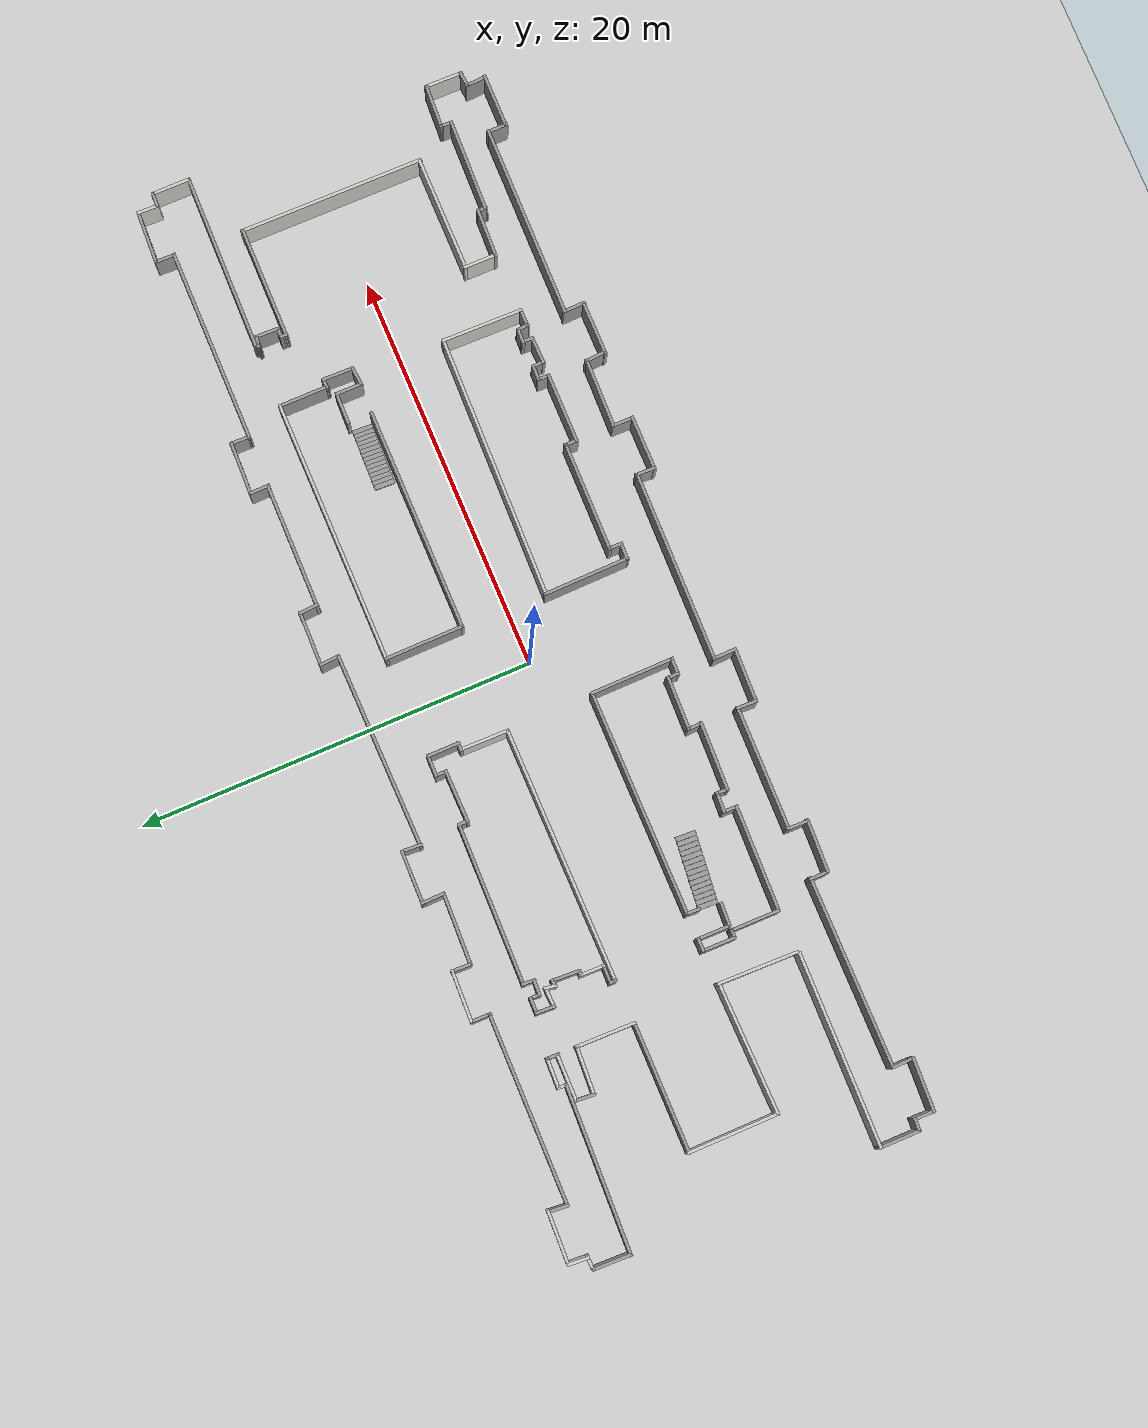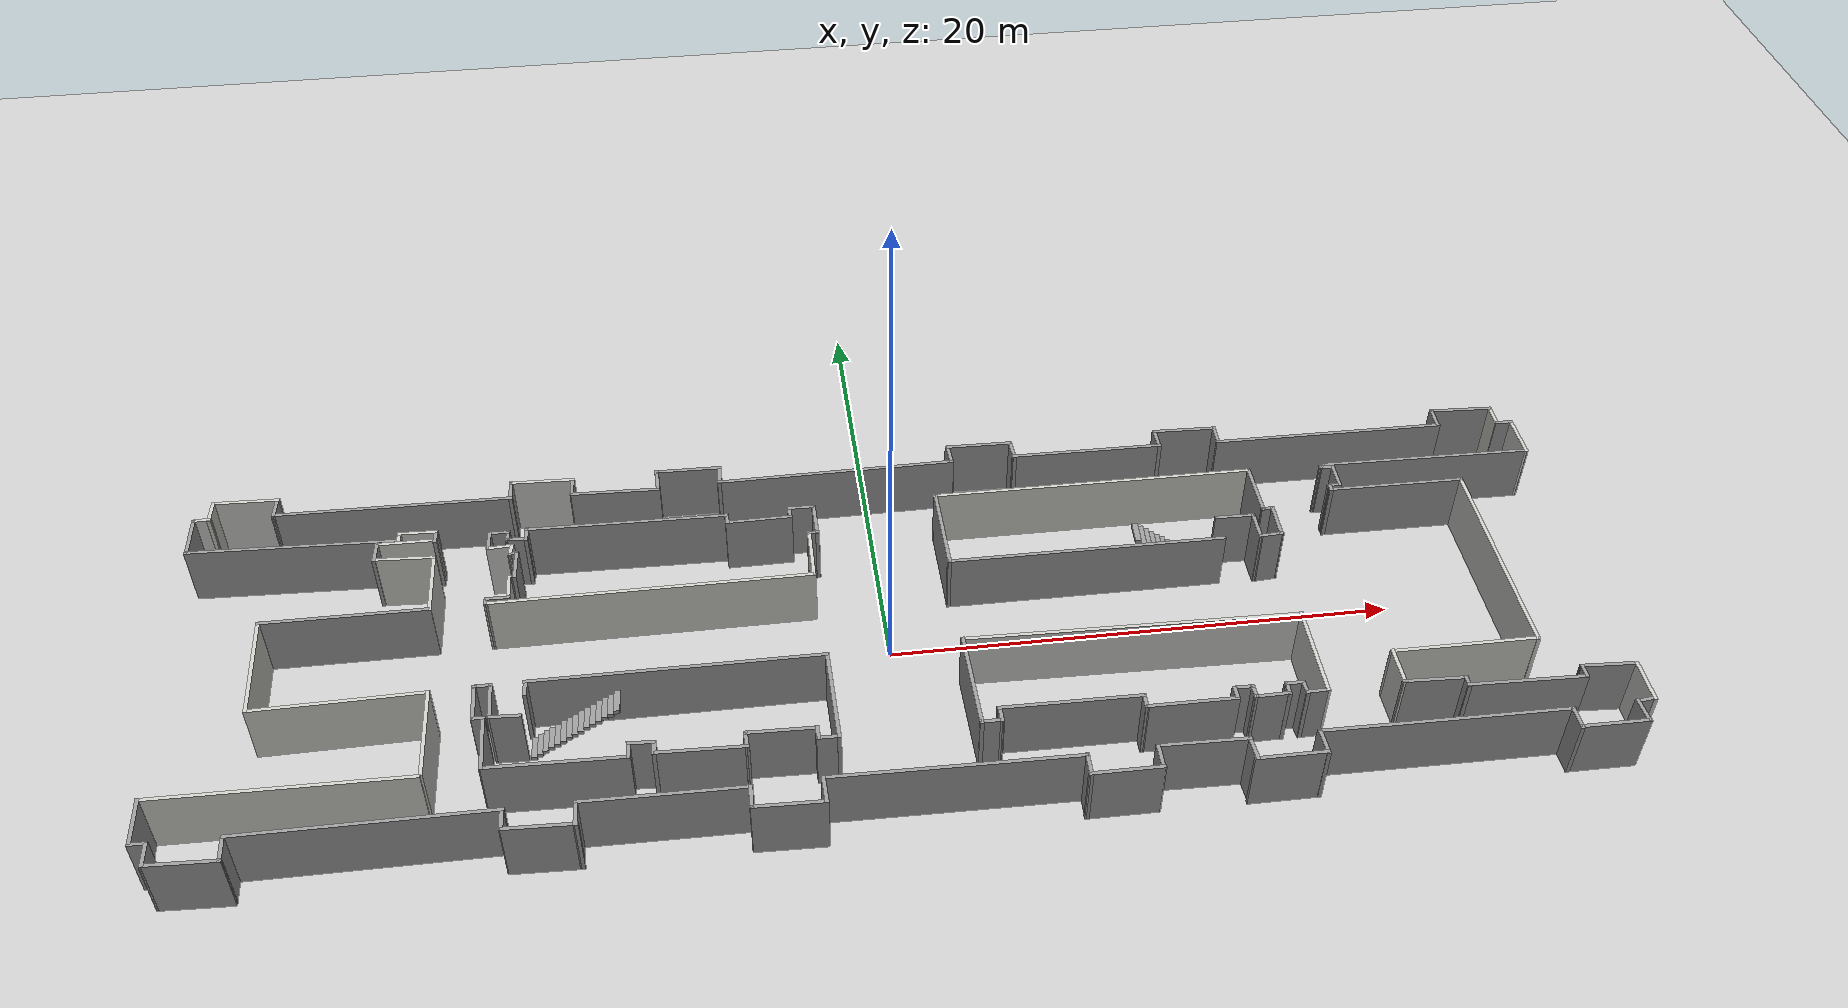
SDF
<sdf version="1.6">
 <world name="default">
  <light name="sun" type="directional">
   <pose>0 0 10 0 -0 0</pose>
   <diffuse>0.8 0.8 0.8 1</diffuse>
   <specular>0.2 0.2 0.2 1</specular>
   <attenuation>
    <range>1000</range>
    <constant>0.9</constant>
    <linear>0.01</linear>
    <quadratic>0.001</quadratic>
   </attenuation>
   <direction>-0.5 0.1 -0.9</direction>
  </light>
  <model name="ground_plane">
   <static>1</static>
   <link name="link">
    <collision name="collision">
     <geometry><plane><normal>0 0 1</normal><size>100 100</size></plane></geometry>
     <surface><friction><ode><mu>100</mu><mu2>50</mu2></ode></friction></surface>
    </collision>
    <visual name="visual">
     <cast_shadows>0</cast_shadows>
     <geometry><plane><normal>0 0 1</normal><size>100 100</size></plane></geometry>
     <material>
      <script><uri>file://media/materials/scripts/gazebo.material</uri><name>Gazebo/Grey</name></script>
     </material>
    </visual>
   </link>
  </model>
  <gravity>0 0 -9.8</gravity>
  <magnetic_field>6e-06 2.3e-05 -4.2e-05</magnetic_field>
  <atmosphere type="adiabatic"/>
  <physics name="default_physics" default="0" type="ode">
   <max_step_size>0.001</max_step_size>
   <real_time_factor>1</real_time_factor>
   <real_time_update_rate>1000</real_time_update_rate>
  </physics>
  <scene><ambient>0.4 0.4 0.4 1</ambient><background>0.7 0.7 0.7 1</background><shadows>1</shadows></scene>
  <spherical_coordinates>
   <surface_model>EARTH_WGS84</surface_model>
   <latitude_deg>0</latitude_deg>
   <longitude_deg>0</longitude_deg>
   <elevation>0</elevation>
   <heading_deg>0</heading_deg>
  </spherical_coordinates>
  <model name="D1">
   <pose>0 0 0 0 0 -0.05</pose>
   <link name="Stairs_2">
    <visual name="Stairs_2_Visual_0">
     <pose>-13.6651 -3.89309 0.083333 0 -0 1.5708</pose>
     <geometry><box><size>1 0.233333 0.166667</size></box></geometry>
     <material>
      <script><uri>file://media/materials/scripts/gazebo.material</uri><name>Gazebo/Grey</name></script>
      <ambient>1 1 1 1</ambient>
     </material>
     <meta><layer>0</layer></meta>
    </visual>
    <collision name="Stairs_2_Collision_0">
     <geometry><box><size>1 0.233333 0.166667</size></box></geometry>
     <pose>-13.6651 -3.89309 0.083333 0 -0 1.5708</pose>
    </collision>
    <visual name="Stairs_2_Visual_1">
     <pose>-13.4318 -3.89309 0.25 0 -0 1.5708</pose>
     <geometry><box><size>1 0.233333 0.166667</size></box></geometry>
     <material>
      <script><uri>file://media/materials/scripts/gazebo.material</uri><name>Gazebo/Grey</name></script>
      <ambient>1 1 1 1</ambient>
     </material>
     <meta><layer>0</layer></meta>
    </visual>
    <collision name="Stairs_2_Collision_1">
     <geometry><box><size>1 0.233333 0.166667</size></box></geometry>
     <pose>-13.4318 -3.89309 0.25 0 -0 1.5708</pose>
    </collision>
    <visual name="Stairs_2_Visual_2">
     <pose>-13.1984 -3.89309 0.416667 0 -0 1.5708</pose>
     <geometry><box><size>1 0.233333 0.166667</size></box></geometry>
     <material>
      <script><uri>file://media/materials/scripts/gazebo.material</uri><name>Gazebo/Grey</name></script>
      <ambient>1 1 1 1</ambient>
     </material>
     <meta><layer>0</layer></meta>
    </visual>
    <collision name="Stairs_2_Collision_2">
     <geometry><box><size>1 0.233333 0.166667</size></box></geometry>
     <pose>-13.1984 -3.89309 0.416667 0 -0 1.5708</pose>
    </collision>
    <visual name="Stairs_2_Visual_3">
     <pose>-12.9651 -3.89309 0.583333 0 -0 1.5708</pose>
     <geometry><box><size>1 0.233333 0.166667</size></box></geometry>
     <material>
      <script><uri>file://media/materials/scripts/gazebo.material</uri><name>Gazebo/Grey</name></script>
      <ambient>1 1 1 1</ambient>
     </material>
     <meta><layer>0</layer></meta>
    </visual>
    <collision name="Stairs_2_Collision_3">
     <geometry><box><size>1 0.233333 0.166667</size></box></geometry>
     <pose>-12.9651 -3.89309 0.583333 0 -0 1.5708</pose>
    </collision>
    <visual name="Stairs_2_Visual_4">
     <pose>-12.7318 -3.89309 0.75 0 -0 1.5708</pose>
     <geometry><box><size>1 0.233333 0.166667</size></box></geometry>
     <material>
      <script><uri>file://media/materials/scripts/gazebo.material</uri><name>Gazebo/Grey</name></script>
      <ambient>1 1 1 1</ambient>
     </material>
     <meta><layer>0</layer></meta>
    </visual>
    <collision name="Stairs_2_Collision_4">
     <geometry><box><size>1 0.233333 0.166667</size></box></geometry>
     <pose>-12.7318 -3.89309 0.75 0 -0 1.5708</pose>
    </collision>
    <visual name="Stairs_2_Visual_5">
     <pose>-12.4984 -3.89309 0.916667 0 -0 1.5708</pose>
     <geometry><box><size>1 0.233333 0.166667</size></box></geometry>
     <material>
      <script><uri>file://media/materials/scripts/gazebo.material</uri><name>Gazebo/Grey</name></script>
      <ambient>1 1 1 1</ambient>
     </material>
     <meta><layer>0</layer></meta>
    </visual>
    <collision name="Stairs_2_Collision_5">
     <geometry><box><size>1 0.233333 0.166667</size></box></geometry>
     <pose>-12.4984 -3.89309 0.916667 0 -0 1.5708</pose>
    </collision>
    <visual name="Stairs_2_Visual_6">
     <pose>-12.2651 -3.89309 1.08333 0 -0 1.5708</pose>
     <geometry><box><size>1 0.233333 0.166667</size></box></geometry>
     <material>
      <script><uri>file://media/materials/scripts/gazebo.material</uri><name>Gazebo/Grey</name></script>
      <ambient>1 1 1 1</ambient>
     </material>
     <meta><layer>0</layer></meta>
    </visual>
    <collision name="Stairs_2_Collision_6">
     <geometry><box><size>1 0.233333 0.166667</size></box></geometry>
     <pose>-12.2651 -3.89309 1.08333 0 -0 1.5708</pose>
    </collision>
    <visual name="Stairs_2_Visual_7">
     <pose>-12.0318 -3.89309 1.25 0 -0 1.5708</pose>
     <geometry><box><size>1 0.233333 0.166667</size></box></geometry>
     <material>
      <script><uri>file://media/materials/scripts/gazebo.material</uri><name>Gazebo/Grey</name></script>
      <ambient>1 1 1 1</ambient>
     </material>
     <meta><layer>0</layer></meta>
    </visual>
    <collision name="Stairs_2_Collision_7">
     <geometry><box><size>1 0.233333 0.166667</size></box></geometry>
     <pose>-12.0318 -3.89309 1.25 0 -0 1.5708</pose>
    </collision>
    <visual name="Stairs_2_Visual_8">
     <pose>-11.7984 -3.89309 1.41667 0 -0 1.5708</pose>
     <geometry><box><size>1 0.233333 0.166667</size></box></geometry>
     <material>
      <script><uri>file://media/materials/scripts/gazebo.material</uri><name>Gazebo/Grey</name></script>
      <ambient>1 1 1 1</ambient>
     </material>
     <meta><layer>0</layer></meta>
    </visual>
    <collision name="Stairs_2_Collision_8">
     <geometry><box><size>1 0.233333 0.166667</size></box></geometry>
     <pose>-11.7984 -3.89309 1.41667 0 -0 1.5708</pose>
    </collision>
    <visual name="Stairs_2_Visual_9">
     <pose>-11.5651 -3.89309 1.58333 0 -0 1.5708</pose>
     <geometry><box><size>1 0.233333 0.166667</size></box></geometry>
     <material>
      <script><uri>file://media/materials/scripts/gazebo.material</uri><name>Gazebo/Grey</name></script>
      <ambient>1 1 1 1</ambient>
     </material>
     <meta><layer>0</layer></meta>
    </visual>
    <collision name="Stairs_2_Collision_9">
     <geometry><box><size>1 0.233333 0.166667</size></box></geometry>
     <pose>-11.5651 -3.89309 1.58333 0 -0 1.5708</pose>
    </collision>
    <visual name="Stairs_2_Visual_10">
     <pose>-11.3318 -3.89309 1.75 0 -0 1.5708</pose>
     <geometry><box><size>1 0.233333 0.166667</size></box></geometry>
     <material>
      <script><uri>file://media/materials/scripts/gazebo.material</uri><name>Gazebo/Grey</name></script>
      <ambient>1 1 1 1</ambient>
     </material>
     <meta><layer>0</layer></meta>
    </visual>
    <collision name="Stairs_2_Collision_10">
     <geometry><box><size>1 0.233333 0.166667</size></box></geometry>
     <pose>-11.3318 -3.89309 1.75 0 -0 1.5708</pose>
    </collision>
    <visual name="Stairs_2_Visual_11">
     <pose>-11.0984 -3.89309 1.91667 0 -0 1.5708</pose>
     <geometry><box><size>1 0.233333 0.166667</size></box></geometry>
     <material>
      <script><uri>file://media/materials/scripts/gazebo.material</uri><name>Gazebo/Grey</name></script>
      <ambient>1 1 1 1</ambient>
     </material>
     <meta><layer>0</layer></meta>
    </visual>
    <collision name="Stairs_2_Collision_11">
     <geometry><box><size>1 0.233333 0.166667</size></box></geometry>
     <pose>-11.0984 -3.89309 1.91667 0 -0 1.5708</pose>
    </collision>
    <visual name="Stairs_2_Visual_12">
     <pose>-10.8651 -3.89309 2.08333 0 -0 1.5708</pose>
     <geometry><box><size>1 0.233333 0.166667</size></box></geometry>
     <material>
      <script><uri>file://media/materials/scripts/gazebo.material</uri><name>Gazebo/Grey</name></script>
      <ambient>1 1 1 1</ambient>
     </material>
     <meta><layer>0</layer></meta>
    </visual>
    <collision name="Stairs_2_Collision_12">
     <geometry><box><size>1 0.233333 0.166667</size></box></geometry>
     <pose>-10.8651 -3.89309 2.08333 0 -0 1.5708</pose>
    </collision>
    <visual name="Stairs_2_Visual_13">
     <pose>-10.6318 -3.89309 2.25 0 -0 1.5708</pose>
     <geometry><box><size>1 0.233333 0.166667</size></box></geometry>
     <material>
      <script><uri>file://media/materials/scripts/gazebo.material</uri><name>Gazebo/Grey</name></script>
      <ambient>1 1 1 1</ambient>
     </material>
     <meta><layer>0</layer></meta>
    </visual>
    <collision name="Stairs_2_Collision_13">
     <geometry><box><size>1 0.233333 0.166667</size></box></geometry>
     <pose>-10.6318 -3.89309 2.25 0 -0 1.5708</pose>
    </collision>
    <visual name="Stairs_2_Visual_14">
     <pose>-10.3984 -3.89309 2.41667 0 -0 1.5708</pose>
     <geometry><box><size>1 0.233333 0.166667</size></box></geometry>
     <material>
      <script><uri>file://media/materials/scripts/gazebo.material</uri><name>Gazebo/Grey</name></script>
      <ambient>1 1 1 1</ambient>
     </material>
     <meta><layer>0</layer></meta>
    </visual>
    <collision name="Stairs_2_Collision_14">
     <geometry><box><size>1 0.233333 0.166667</size></box></geometry>
     <pose>-10.3984 -3.89309 2.41667 0 -0 1.5708</pose>
    </collision>
   </link>
   <link name="Stairs_3">
    <visual name="Stairs_3_Visual_0">
     <pose>13.3899 3.65816 0.083333 0 -0 -1.5708</pose>
     <geometry><box><size>1 0.233333 0.166667</size></box></geometry>
     <material>
      <script><uri>file://media/materials/scripts/gazebo.material</uri><name>Gazebo/Grey</name></script>
      <ambient>1 1 1 1</ambient>
     </material>
     <meta><layer>0</layer></meta>
    </visual>
    <collision name="Stairs_3_Collision_0">
     <geometry><box><size>1 0.233333 0.166667</size></box></geometry>
     <pose>13.3899 3.65816 0.083333 0 -0 -1.5708</pose>
    </collision>
    <visual name="Stairs_3_Visual_1">
     <pose>13.1565 3.65816 0.25 0 -0 -1.5708</pose>
     <geometry><box><size>1 0.233333 0.166667</size></box></geometry>
     <material>
      <script><uri>file://media/materials/scripts/gazebo.material</uri><name>Gazebo/Grey</name></script>
      <ambient>1 1 1 1</ambient>
     </material>
     <meta><layer>0</layer></meta>
    </visual>
    <collision name="Stairs_3_Collision_1">
     <geometry><box><size>1 0.233333 0.166667</size></box></geometry>
     <pose>13.1565 3.65816 0.25 0 -0 -1.5708</pose>
    </collision>
    <visual name="Stairs_3_Visual_2">
     <pose>12.9232 3.65816 0.416667 0 -0 -1.5708</pose>
     <geometry><box><size>1 0.233333 0.166667</size></box></geometry>
     <material>
      <script><uri>file://media/materials/scripts/gazebo.material</uri><name>Gazebo/Grey</name></script>
      <ambient>1 1 1 1</ambient>
     </material>
     <meta><layer>0</layer></meta>
    </visual>
    <collision name="Stairs_3_Collision_2">
     <geometry><box><size>1 0.233333 0.166667</size></box></geometry>
     <pose>12.9232 3.65816 0.416667 0 -0 -1.5708</pose>
    </collision>
    <visual name="Stairs_3_Visual_3">
     <pose>12.6899 3.65816 0.583333 0 -0 -1.5708</pose>
     <geometry><box><size>1 0.233333 0.166667</size></box></geometry>
     <material>
      <script><uri>file://media/materials/scripts/gazebo.material</uri><name>Gazebo/Grey</name></script>
      <ambient>1 1 1 1</ambient>
     </material>
     <meta><layer>0</layer></meta>
    </visual>
    <collision name="Stairs_3_Collision_3">
     <geometry><box><size>1 0.233333 0.166667</size></box></geometry>
     <pose>12.6899 3.65816 0.583333 0 -0 -1.5708</pose>
    </collision>
    <visual name="Stairs_3_Visual_4">
     <pose>12.4565 3.65816 0.75 0 -0 -1.5708</pose>
     <geometry><box><size>1 0.233333 0.166667</size></box></geometry>
     <material>
      <script><uri>file://media/materials/scripts/gazebo.material</uri><name>Gazebo/Grey</name></script>
      <ambient>1 1 1 1</ambient>
     </material>
     <meta><layer>0</layer></meta>
    </visual>
    <collision name="Stairs_3_Collision_4">
     <geometry><box><size>1 0.233333 0.166667</size></box></geometry>
     <pose>12.4565 3.65816 0.75 0 -0 -1.5708</pose>
    </collision>
    <visual name="Stairs_3_Visual_5">
     <pose>12.2232 3.65816 0.916667 0 -0 -1.5708</pose>
     <geometry><box><size>1 0.233333 0.166667</size></box></geometry>
     <material>
      <script><uri>file://media/materials/scripts/gazebo.material</uri><name>Gazebo/Grey</name></script>
      <ambient>1 1 1 1</ambient>
     </material>
     <meta><layer>0</layer></meta>
    </visual>
    <collision name="Stairs_3_Collision_5">
     <geometry><box><size>1 0.233333 0.166667</size></box></geometry>
     <pose>12.2232 3.65816 0.916667 0 -0 -1.5708</pose>
    </collision>
    <visual name="Stairs_3_Visual_6">
     <pose>11.9899 3.65816 1.08333 0 -0 -1.5708</pose>
     <geometry><box><size>1 0.233333 0.166667</size></box></geometry>
     <material>
      <script><uri>file://media/materials/scripts/gazebo.material</uri><name>Gazebo/Grey</name></script>
      <ambient>1 1 1 1</ambient>
     </material>
     <meta><layer>0</layer></meta>
    </visual>
    <collision name="Stairs_3_Collision_6">
     <geometry><box><size>1 0.233333 0.166667</size></box></geometry>
     <pose>11.9899 3.65816 1.08333 0 -0 -1.5708</pose>
    </collision>
    <visual name="Stairs_3_Visual_7">
     <pose>11.7565 3.65816 1.25 0 -0 -1.5708</pose>
     <geometry><box><size>1 0.233333 0.166667</size></box></geometry>
     <material>
      <script><uri>file://media/materials/scripts/gazebo.material</uri><name>Gazebo/Grey</name></script>
      <ambient>1 1 1 1</ambient>
     </material>
     <meta><layer>0</layer></meta>
    </visual>
    <collision name="Stairs_3_Collision_7">
     <geometry><box><size>1 0.233333 0.166667</size></box></geometry>
     <pose>11.7565 3.65816 1.25 0 -0 -1.5708</pose>
    </collision>
    <visual name="Stairs_3_Visual_8">
     <pose>11.5232 3.65816 1.41667 0 -0 -1.5708</pose>
     <geometry><box><size>1 0.233333 0.166667</size></box></geometry>
     <material>
      <script><uri>file://media/materials/scripts/gazebo.material</uri><name>Gazebo/Grey</name></script>
      <ambient>1 1 1 1</ambient>
     </material>
     <meta><layer>0</layer></meta>
    </visual>
    <collision name="Stairs_3_Collision_8">
     <geometry><box><size>1 0.233333 0.166667</size></box></geometry>
     <pose>11.5232 3.65816 1.41667 0 -0 -1.5708</pose>
    </collision>
    <visual name="Stairs_3_Visual_9">
     <pose>11.2899 3.65816 1.58333 0 -0 -1.5708</pose>
     <geometry><box><size>1 0.233333 0.166667</size></box></geometry>
     <material>
      <script><uri>file://media/materials/scripts/gazebo.material</uri><name>Gazebo/Grey</name></script>
      <ambient>1 1 1 1</ambient>
     </material>
     <meta><layer>0</layer></meta>
    </visual>
    <collision name="Stairs_3_Collision_9">
     <geometry><box><size>1 0.233333 0.166667</size></box></geometry>
     <pose>11.2899 3.65816 1.58333 0 -0 -1.5708</pose>
    </collision>
    <visual name="Stairs_3_Visual_10">
     <pose>11.0565 3.65816 1.75 0 -0 -1.5708</pose>
     <geometry><box><size>1 0.233333 0.166667</size></box></geometry>
     <material>
      <script><uri>file://media/materials/scripts/gazebo.material</uri><name>Gazebo/Grey</name></script>
      <ambient>1 1 1 1</ambient>
     </material>
     <meta><layer>0</layer></meta>
    </visual>
    <collision name="Stairs_3_Collision_10">
     <geometry><box><size>1 0.233333 0.166667</size></box></geometry>
     <pose>11.0565 3.65816 1.75 0 -0 -1.5708</pose>
    </collision>
    <visual name="Stairs_3_Visual_11">
     <pose>10.8232 3.65816 1.91667 0 -0 -1.5708</pose>
     <geometry><box><size>1 0.233333 0.166667</size></box></geometry>
     <material>
      <script><uri>file://media/materials/scripts/gazebo.material</uri><name>Gazebo/Grey</name></script>
      <ambient>1 1 1 1</ambient>
     </material>
     <meta><layer>0</layer></meta>
    </visual>
    <collision name="Stairs_3_Collision_11">
     <geometry><box><size>1 0.233333 0.166667</size></box></geometry>
     <pose>10.8232 3.65816 1.91667 0 -0 -1.5708</pose>
    </collision>
    <visual name="Stairs_3_Visual_12">
     <pose>10.5899 3.65816 2.08333 0 -0 -1.5708</pose>
     <geometry><box><size>1 0.233333 0.166667</size></box></geometry>
     <material>
      <script><uri>file://media/materials/scripts/gazebo.material</uri><name>Gazebo/Grey</name></script>
      <ambient>1 1 1 1</ambient>
     </material>
     <meta><layer>0</layer></meta>
    </visual>
    <collision name="Stairs_3_Collision_12">
     <geometry><box><size>1 0.233333 0.166667</size></box></geometry>
     <pose>10.5899 3.65816 2.08333 0 -0 -1.5708</pose>
    </collision>
    <visual name="Stairs_3_Visual_13">
     <pose>10.3565 3.65816 2.25 0 -0 -1.5708</pose>
     <geometry><box><size>1 0.233333 0.166667</size></box></geometry>
     <material>
      <script><uri>file://media/materials/scripts/gazebo.material</uri><name>Gazebo/Grey</name></script>
      <ambient>1 1 1 1</ambient>
     </material>
     <meta><layer>0</layer></meta>
    </visual>
    <collision name="Stairs_3_Collision_13">
     <geometry><box><size>1 0.233333 0.166667</size></box></geometry>
     <pose>10.3565 3.65816 2.25 0 -0 -1.5708</pose>
    </collision>
    <visual name="Stairs_3_Visual_14">
     <pose>10.1232 3.65816 2.41667 0 -0 -1.5708</pose>
     <geometry><box><size>1 0.233333 0.166667</size></box></geometry>
     <material>
      <script><uri>file://media/materials/scripts/gazebo.material</uri><name>Gazebo/Grey</name></script>
      <ambient>1 1 1 1</ambient>
     </material>
     <meta><layer>0</layer></meta>
    </visual>
    <collision name="Stairs_3_Collision_14">
     <geometry><box><size>1 0.233333 0.166667</size></box></geometry>
     <pose>10.1232 3.65816 2.41667 0 -0 -1.5708</pose>
    </collision>
   </link>
   <link name="Wall_10">
    <collision name="Wall_10_Collision">
     <geometry><box><size>4.63207 0.15 2.5</size></box></geometry>
     <pose>0 0 1.25 0 -0 0</pose>
    </collision>
    <visual name="Wall_10_Visual">
     <pose>0 0 1.25 0 -0 0</pose>
     <geometry><box><size>4.63207 0.15 2.5</size></box></geometry>
     <material>
      <script><uri>file://media/materials/scripts/gazebo.material</uri><name>Gazebo/CeilingTiled</name></script>
      <ambient>1 1 1 1</ambient>
     </material>
     <meta><layer>0</layer></meta>
    </visual>
    <pose>-24.0592 -1.13338 0 0 -0 1.62653</pose>
   </link>
   <link name="Wall_100">
    <collision name="Wall_100_Collision">
     <geometry><box><size>0.773484 0.15 2.5</size></box></geometry>
     <pose>0 0 1.25 0 -0 0</pose>
    </collision>
    <visual name="Wall_100_Visual">
     <pose>0 0 1.25 0 -0 0</pose>
     <geometry><box><size>0.773484 0.15 2.5</size></box></geometry>
     <material>
      <script><uri>file://media/materials/scripts/gazebo.material</uri><name>Gazebo/Grey</name></script>
      <ambient>1 1 1 1</ambient>
     </material>
     <meta><layer>0</layer></meta>
    </visual>
    <pose>-9.92754 -6.2916 0 0 -0 1.61902</pose>
   </link>
   <link name="Wall_101">
    <collision name="Wall_101_Collision">
     <geometry><box><size>1.06746 0.15 2.5</size></box></geometry>
     <pose>0 0 1.25 0 -0 0</pose>
    </collision>
    <visual name="Wall_101_Visual">
     <pose>0 0 1.25 0 -0 0</pose>
     <geometry><box><size>1.06746 0.15 2.5</size></box></geometry>
     <material>
      <script><uri>file://media/materials/scripts/gazebo.material</uri><name>Gazebo/Grey</name></script>
      <ambient>1 1 1 1</ambient>
     </material>
     <meta><layer>0</layer></meta>
    </visual>
    <pose>-9.47888 -5.97978 0 0 -0 0.000275</pose>
   </link>
   <link name="Wall_102">
    <collision name="Wall_102_Collision">
     <geometry><box><size>0.675474 0.15 2.5</size></box></geometry>
     <pose>0 0 1.25 0 -0 0</pose>
    </collision>
    <visual name="Wall_102_Visual">
     <pose>0 0 1.25 0 -0 0</pose>
     <geometry><box><size>0.675474 0.15 2.5</size></box></geometry>
     <material>
      <script><uri>file://media/materials/scripts/gazebo.material</uri><name>Gazebo/Grey</name></script>
      <ambient>1 1 1 1</ambient>
     </material>
     <meta><layer>0</layer></meta>
    </visual>
    <pose>-9.01233 -6.23741 0 0 0 -1.55994</pose>
   </link>
   <link name="Wall_103">
    <collision name="Wall_103_Collision">
     <geometry><box><size>3.49404 0.15 2.5</size></box></geometry>
     <pose>0 0 1.25 0 -0 0</pose>
    </collision>
    <visual name="Wall_103_Visual">
     <pose>0 0 1.25 0 -0 0</pose>
     <geometry><box><size>3.49404 0.15 2.5</size></box></geometry>
     <material>
      <script><uri>file://media/materials/scripts/gazebo.material</uri><name>Gazebo/Grey</name></script>
      <ambient>1 1 1 1</ambient>
     </material>
     <meta><layer>0</layer></meta>
    </visual>
    <pose>-7.33774 -6.4603 0 0 -0 0.018625</pose>
   </link>
   <link name="Wall_104">
    <collision name="Wall_104_Collision">
     <geometry><box><size>0.795236 0.15 2.5</size></box></geometry>
     <pose>0 0 1.25 0 -0 0</pose>
    </collision>
    <visual name="Wall_104_Visual">
     <pose>0 0 1.25 0 -0 0</pose>
     <geometry><box><size>0.795236 0.15 2.5</size></box></geometry>
     <material>
      <script><uri>file://media/materials/scripts/gazebo.material</uri><name>Gazebo/Grey</name></script>
      <ambient>1 1 1 1</ambient>
     </material>
     <meta><layer>0</layer></meta>
    </visual>
    <pose>-5.70354 -6.10783 0 0 -0 1.66029</pose>
   </link>
   <link name="Wall_105">
    <collision name="Wall_105_Collision">
     <geometry><box><size>2.73731 0.15 2.5</size></box></geometry>
     <pose>0 0 1.25 0 -0 0</pose>
    </collision>
    <visual name="Wall_105_Visual">
     <pose>0 0 1.25 0 -0 0</pose>
     <geometry><box><size>2.73731 0.15 2.5</size></box></geometry>
     <material>
      <script><uri>file://media/materials/scripts/gazebo.material</uri><name>Gazebo/Grey</name></script>
      <ambient>1 1 1 1</ambient>
     </material>
     <meta><layer>0</layer></meta>
    </visual>
    <pose>-4.43039 -5.76472 0 0 -0 0.023559</pose>
   </link>
   <link name="Wall_106">
    <collision name="Wall_106_Collision">
     <geometry><box><size>0.653616 0.15 2.5</size></box></geometry>
     <pose>0 0 1.25 0 -0 0</pose>
    </collision>
    <visual name="Wall_106_Visual">
     <pose>0 0 1.25 0 -0 0</pose>
     <geometry><box><size>0.653616 0.15 2.5</size></box></geometry>
     <material>
      <script><uri>file://media/materials/scripts/gazebo.material</uri><name>Gazebo/Grey</name></script>
      <ambient>1 1 1 1</ambient>
     </material>
     <meta><layer>0</layer></meta>
    </visual>
    <pose>-3.11506 -5.96831 0 0 0 -1.51781</pose>
   </link>
   <link name="Wall_107">
    <collision name="Wall_107_Collision">
     <geometry><box><size>0.894241 0.15 2.5</size></box></geometry>
     <pose>0 0 1.25 0 -0 0</pose>
    </collision>
    <visual name="Wall_107_Visual">
     <pose>0 0 1.25 0 -0 0</pose>
     <geometry><box><size>0.894241 0.15 2.5</size></box></geometry>
     <material>
      <script><uri>file://media/materials/scripts/gazebo.material</uri><name>Gazebo/Grey</name></script>
      <ambient>1 1 1 1</ambient>
     </material>
     <meta><layer>0</layer></meta>
    </visual>
    <pose>-2.72968 -6.2144 0 0 -0 0.037791</pose>
   </link>
   <link name="Wall_108">
    <collision name="Wall_108_Collision">
     <geometry><box><size>4.24433 0.15 2.5</size></box></geometry>
     <pose>0 0 1.25 0 -0 0</pose>
    </collision>
    <visual name="Wall_108_Visual">
     <pose>0 0 1.25 0 -0 0</pose>
     <geometry><box><size>4.24433 0.15 2.5</size></box></geometry>
     <material>
      <script><uri>file://media/materials/scripts/gazebo.material</uri><name>Gazebo/Grey</name></script>
      <ambient>1 1 1 1</ambient>
     </material>
     <meta><layer>0</layer></meta>
    </visual>
    <pose>-2.46576 -4.1652 0 0 -0 1.62789</pose>
   </link>
   <link name="Wall_109">
    <collision name="Wall_109_Collision">
     <geometry><box><size>11.3689 0.15 2.5</size></box></geometry>
     <pose>0 0 1.25 0 -0 0</pose>
    </collision>
    <visual name="Wall_109_Visual">
     <pose>0 0 1.25 0 -0 0</pose>
     <geometry><box><size>11.3689 0.15 2.5</size></box></geometry>
     <material>
      <script><uri>file://media/materials/scripts/gazebo.material</uri><name>Gazebo/Grey</name></script>
      <ambient>1 1 1 1</ambient>
     </material>
     <meta><layer>0</layer></meta>
    </visual>
    <pose>-8.22003 -2.40121 0 0 0 -3.09169</pose>
   </link>
   <link name="Wall_11">
    <collision name="Wall_11_Collision">
     <geometry><box><size>6.62047 0.15 2.5</size></box></geometry>
     <pose>0 0 1.25 0 -0 0</pose>
    </collision>
    <visual name="Wall_11_Visual">
     <pose>0 0 1.25 0 -0 0</pose>
     <geometry><box><size>6.62047 0.15 2.5</size></box></geometry>
     <material>
      <script><uri>file://media/materials/scripts/gazebo.material</uri><name>Gazebo/Grey</name></script>
      <ambient>1 1 1 1</ambient>
     </material>
     <meta><layer>0</layer></meta>
    </visual>
    <pose>-20.9609 1.24512 0 0 -0 0.046255</pose>
   </link>
   <link name="Wall_111">
    <collision name="Wall_111_Collision">
     <geometry><box><size>1.25 0.15 2.5</size></box></geometry>
     <pose>0 0 1.25 0 -0 0</pose>
    </collision>
    <visual name="Wall_111_Visual">
     <pose>0 0 1.25 0 -0 0</pose>
     <geometry><box><size>1.25 0.15 2.5</size></box></geometry>
     <material>
      <script><uri>file://media/materials/scripts/gazebo.material</uri><name>Gazebo/Grey</name></script>
      <ambient>1 1 1 1</ambient>
     </material>
     <meta><layer>0</layer></meta>
    </visual>
    <pose>-14.4644 -4.34643 0 0 -0 3.14159</pose>
   </link>
   <link name="Wall_112">
    <collision name="Wall_112_Collision">
     <geometry><box><size>1.75537 0.15 2.5</size></box></geometry>
     <pose>0 0 1.25 0 -0 0</pose>
    </collision>
    <visual name="Wall_112_Visual">
     <pose>0 0 1.25 0 -0 0</pose>
     <geometry><box><size>1.75537 0.15 2.5</size></box></geometry>
     <material>
      <script><uri>file://media/materials/scripts/gazebo.material</uri><name>Gazebo/Grey</name></script>
      <ambient>1 1 1 1</ambient>
     </material>
     <meta><layer>0</layer></meta>
    </visual>
    <pose>-15.0589 -3.54472 0 0 -0 1.61397</pose>
   </link>
   <link name="Wall_113">
    <collision name="Wall_113_Collision">
     <geometry><box><size>0.708313 0.15 2.5</size></box></geometry>
     <pose>0 0 1.25 0 -0 0</pose>
    </collision>
    <visual name="Wall_113_Visual">
     <pose>0 0 1.25 0 -0 0</pose>
     <geometry><box><size>0.708313 0.15 2.5</size></box></geometry>
     <material>
      <script><uri>file://media/materials/scripts/gazebo.material</uri><name>Gazebo/Grey</name></script>
      <ambient>1 1 1 1</ambient>
     </material>
     <meta><layer>0</layer></meta>
    </visual>
    <pose>-15.3899 -2.77455 0 0 0 -3.09124</pose>
   </link>
   <link name="Wall_114">
    <collision name="Wall_114_Collision">
     <geometry><box><size>1.69753 0.15 2.5</size></box></geometry>
     <pose>0 0 1.25 0 -0 0</pose>
    </collision>
    <visual name="Wall_114_Visual">
     <pose>0 0 1.25 0 -0 0</pose>
     <geometry><box><size>1.69753 0.15 2.5</size></box></geometry>
     <material>
      <script><uri>file://media/materials/scripts/gazebo.material</uri><name>Gazebo/Grey</name></script>
      <ambient>1 1 1 1</ambient>
     </material>
     <meta><layer>0</layer></meta>
    </visual>
    <pose>-15.6542 -3.5792 0 0 0 -1.52945</pose>
   </link>
   <link name="Wall_115">
    <collision name="Wall_115_Collision">
     <geometry><box><size>0.518108 0.15 2.5</size></box></geometry>
     <pose>0 0 1.25 0 -0 0</pose>
    </collision>
    <visual name="Wall_115_Visual">
     <pose>0 0 1.25 0 -0 0</pose>
     <geometry><box><size>0.518108 0.15 2.5</size></box></geometry>
     <material>
      <script><uri>file://media/materials/scripts/gazebo.material</uri><name>Gazebo/Grey</name></script>
      <ambient>1 1 1 1</ambient>
     </material>
     <meta><layer>0</layer></meta>
    </visual>
    <pose>-15.4207 -4.36883 0 0 -0 0.005204</pose>
   </link>
   <link name="Wall_118">
    <collision name="Wall_118_Collision">
     <geometry><box><size>2.52729 0.15 2.5</size></box></geometry>
     <pose>0 0 1.25 0 -0 0</pose>
    </collision>
    <visual name="Wall_118_Visual">
     <pose>0 0 1.25 0 -0 0</pose>
     <geometry><box><size>2.52729 0.15 2.5</size></box></geometry>
     <material>
      <script><uri>file://media/materials/scripts/gazebo.material</uri><name>Gazebo/Grey</name></script>
      <ambient>1 1 1 1</ambient>
     </material>
     <meta><layer>0</layer></meta>
    </visual>
    <pose>-15.1971 -5.55554 0 0 -0 1.61876</pose>
   </link>
   <link name="Wall_120">
    <collision name="Wall_120_Collision">
     <geometry><box><size>4.36198 0.15 2.5</size></box></geometry>
     <pose>0 0 1.25 0 -0 0</pose>
    </collision>
    <visual name="Wall_120_Visual">
     <pose>0 0 1.25 0 -0 0</pose>
     <geometry><box><size>4.36198 0.15 2.5</size></box></geometry>
     <material>
      <script><uri>file://media/materials/scripts/gazebo.material</uri><name>Gazebo/Grey</name></script>
      <ambient>1 1 1 1</ambient>
     </material>
     <meta><layer>0</layer></meta>
    </visual>
    <pose>2.72249 -3.79955 0 0 0 -1.50734</pose>
   </link>
   <link name="Wall_121">
    <collision name="Wall_121_Collision">
     <geometry><box><size>0.873507 0.15 2.5</size></box></geometry>
     <pose>0 0 1.25 0 -0 0</pose>
    </collision>
    <visual name="Wall_121_Visual">
     <pose>0 0 1.25 0 -0 0</pose>
     <geometry><box><size>0.873507 0.15 2.5</size></box></geometry>
     <material>
      <script><uri>file://media/materials/scripts/gazebo.material</uri><name>Gazebo/Grey</name></script>
      <ambient>1 1 1 1</ambient>
     </material>
     <meta><layer>0</layer></meta>
    </visual>
    <pose>3.21778 -5.87986 0 0 -0 0.004303</pose>
   </link>
   <link name="Wall_122">
    <collision name="Wall_122_Collision">
     <geometry><box><size>0.750329 0.15 2.5</size></box></geometry>
     <pose>0 0 1.25 0 -0 0</pose>
    </collision>
    <visual name="Wall_122_Visual">
     <pose>0 0 1.25 0 -0 0</pose>
     <geometry><box><size>0.750329 0.15 2.5</size></box></geometry>
     <material>
      <script><uri>file://media/materials/scripts/gazebo.material</uri><name>Gazebo/Grey</name></script>
      <ambient>1 1 1 1</ambient>
     </material>
     <meta><layer>0</layer></meta>
    </visual>
    <pose>3.59259 -5.5783 0 0 -0 1.60393</pose>
   </link>
   <link name="Wall_123">
    <collision name="Wall_123_Collision">
     <geometry><box><size>5.55126 0.15 2.5</size></box></geometry>
     <pose>0 0 1.25 0 -0 0</pose>
    </collision>
    <visual name="Wall_123_Visual">
     <pose>0 0 1.25 0 -0 0</pose>
     <geometry><box><size>5.55126 0.15 2.5</size></box></geometry>
     <material>
      <script><uri>file://media/materials/scripts/gazebo.material</uri><name>Gazebo/Grey</name></script>
      <ambient>1 1 1 1</ambient>
     </material>
     <meta><layer>0</layer></meta>
    </visual>
    <pose>6.25812 -5.17048 0 0 -0 0.039936</pose>
   </link>
   <link name="Wall_124">
    <collision name="Wall_124_Collision">
     <geometry><box><size>0.673913 0.15 2.5</size></box></geometry>
     <pose>0 0 1.25 0 -0 0</pose>
    </collision>
    <visual name="Wall_124_Visual">
     <pose>0 0 1.25 0 -0 0</pose>
     <geometry><box><size>0.673913 0.15 2.5</size></box></geometry>
     <material>
      <script><uri>file://media/materials/scripts/gazebo.material</uri><name>Gazebo/Grey</name></script>
      <ambient>1 1 1 1</ambient>
     </material>
     <meta><layer>0</layer></meta>
    </visual>
    <pose>8.9639 -5.3444 0 0 0 -1.5429</pose>
   </link>
   <link name="Wall_125">
    <collision name="Wall_125_Collision">
     <geometry><box><size>3.54447 0.15 2.5</size></box></geometry>
     <pose>0 0 1.25 0 -0 0</pose>
    </collision>
    <visual name="Wall_125_Visual">
     <pose>0 0 1.25 0 -0 0</pose>
     <geometry><box><size>3.54447 0.15 2.5</size></box></geometry>
     <material>
      <script><uri>file://media/materials/scripts/gazebo.material</uri><name>Gazebo/Grey</name></script>
      <ambient>1 1 1 1</ambient>
     </material>
     <meta><layer>0</layer></meta>
    </visual>
    <pose>10.6782 -5.52934 0 0 -0 0.045331</pose>
   </link>
   <link name="Wall_126">
    <collision name="Wall_126_Collision">
     <geometry><box><size>0.650676 0.15 2.5</size></box></geometry>
     <pose>0 0 1.25 0 -0 0</pose>
    </collision>
    <visual name="Wall_126_Visual">
     <pose>0 0 1.25 0 -0 0</pose>
     <geometry><box><size>0.650676 0.15 2.5</size></box></geometry>
     <material>
      <script><uri>file://media/materials/scripts/gazebo.material</uri><name>Gazebo/Grey</name></script>
      <ambient>1 1 1 1</ambient>
     </material>
     <meta><layer>0</layer></meta>
    </visual>
    <pose>12.3627 -5.19065 0 0 -0 1.61481</pose>
   </link>
   <link name="Wall_127">
    <collision name="Wall_127_Collision">
     <geometry><box><size>0.829635 0.15 2.5</size></box></geometry>
     <pose>0 0 1.25 0 -0 0</pose>
    </collision>
    <visual name="Wall_127_Visual">
     <pose>0 0 1.25 0 -0 0</pose>
     <geometry><box><size>0.829635 0.15 2.5</size></box></geometry>
     <material>
      <script><uri>file://media/materials/scripts/gazebo.material</uri><name>Gazebo/Grey</name></script>
      <ambient>1 1 1 1</ambient>
     </material>
     <meta><layer>0</layer></meta>
    </visual>
    <pose>12.7028 -4.9315 0 0 -0 0.026084</pose>
   </link>
   <link name="Wall_128">
    <collision name="Wall_128_Collision">
     <geometry><box><size>0.662976 0.15 2.5</size></box></geometry>
     <pose>0 0 1.25 0 -0 0</pose>
    </collision>
    <visual name="Wall_128_Visual">
     <pose>0 0 1.25 0 -0 0</pose>
     <geometry><box><size>0.662976 0.15 2.5</size></box></geometry>
     <material>
      <script><uri>file://media/materials/scripts/gazebo.material</uri><name>Gazebo/Grey</name></script>
      <ambient>1 1 1 1</ambient>
     </material>
     <meta><layer>0</layer></meta>
    </visual>
    <pose>13.0551 -5.178 0 0 0 -1.47677</pose>
   </link>
   <link name="Wall_129">
    <collision name="Wall_129_Collision">
     <geometry><box><size>1.41196 0.15 2.5</size></box></geometry>
     <pose>0 0 1.25 0 -0 0</pose>
    </collision>
    <visual name="Wall_129_Visual">
     <pose>0 0 1.25 0 -0 0</pose>
     <geometry><box><size>1.41196 0.15 2.5</size></box></geometry>
     <material>
      <script><uri>file://media/materials/scripts/gazebo.material</uri><name>Gazebo/Grey</name></script>
      <ambient>1 1 1 1</ambient>
     </material>
     <meta><layer>0</layer></meta>
    </visual>
    <pose>13.6977 -5.39163 0 0 -0 0.06613</pose>
   </link>
   <link name="Wall_130">
    <collision name="Wall_130_Collision">
     <geometry><box><size>0.650966 0.15 2.5</size></box></geometry>
     <pose>0 0 1.25 0 -0 0</pose>
    </collision>
    <visual name="Wall_130_Visual">
     <pose>0 0 1.25 0 -0 0</pose>
     <geometry><box><size>0.650966 0.15 2.5</size></box></geometry>
     <material>
      <script><uri>file://media/materials/scripts/gazebo.material</uri><name>Gazebo/Grey</name></script>
      <ambient>1 1 1 1</ambient>
     </material>
     <meta><layer>0</layer></meta>
    </visual>
    <pose>14.3289 -5.11093 0 0 -0 1.56561</pose>
   </link>
   <link name="Wall_131">
    <collision name="Wall_131_Collision">
     <geometry><box><size>0.765829 0.15 2.5</size></box></geometry>
     <pose>0 0 1.25 0 -0 0</pose>
    </collision>
    <visual name="Wall_131_Visual">
     <pose>0 0 1.25 0 -0 0</pose>
     <geometry><box><size>0.765829 0.15 2.5</size></box></geometry>
     <material>
      <script><uri>file://media/materials/scripts/gazebo.material</uri><name>Gazebo/Grey</name></script>
      <ambient>1 1 1 1</ambient>
     </material>
     <meta><layer>0</layer></meta>
    </visual>
    <pose>14.6265 -4.86512 0 0 -0 0.022185</pose>
   </link>
   <link name="Wall_132">
    <collision name="Wall_132_Collision">
     <geometry><box><size>0.650914 0.15 2.5</size></box></geometry>
     <pose>0 0 1.25 0 -0 0</pose>
    </collision>
    <visual name="Wall_132_Visual">
     <pose>0 0 1.25 0 -0 0</pose>
     <geometry><box><size>0.650914 0.15 2.5</size></box></geometry>
     <material>
      <script><uri>file://media/materials/scripts/gazebo.material</uri><name>Gazebo/Grey</name></script>
      <ambient>1 1 1 1</ambient>
     </material>
     <meta><layer>0</layer></meta>
    </visual>
    <pose>14.9748 -5.10708 0 0 0 -1.45518</pose>
   </link>
   <link name="Wall_133">
    <collision name="Wall_133_Collision">
     <geometry><box><size>0.92994 0.15 2.5</size></box></geometry>
     <pose>0 0 1.25 0 -0 0</pose>
    </collision>
    <visual name="Wall_133_Visual">
     <pose>0 0 1.25 0 -0 0</pose>
     <geometry><box><size>0.92994 0.15 2.5</size></box></geometry>
     <material>
      <script><uri>file://media/materials/scripts/gazebo.material</uri><name>Gazebo/Grey</name></script>
      <ambient>1 1 1 1</ambient>
     </material>
     <meta><layer>0</layer></meta>
    </visual>
    <pose>15.3926 -5.31609 0 0 -0 0.072567</pose>
   </link>
   <link name="Wall_134">
    <collision name="Wall_134_Collision">
     <geometry><box><size>4.10517 0.15 2.5</size></box></geometry>
     <pose>0 0 1.25 0 -0 0</pose>
    </collision>
    <visual name="Wall_134_Visual">
     <pose>0 0 1.25 0 -0 0</pose>
     <geometry><box><size>4.10517 0.15 2.5</size></box></geometry>
     <material>
      <script><uri>file://media/materials/scripts/gazebo.material</uri><name>Gazebo/CeilingTiled</name></script>
      <ambient>1 1 1 1</ambient>
     </material>
     <meta><layer>0</layer></meta>
    </visual>
    <pose>15.7356 -3.31106 0 0 -0 1.59988</pose>
   </link>
   <link name="Wall_137">
    <collision name="Wall_137_Collision">
     <geometry><box><size>12.87 0.15 2.5</size></box></geometry>
     <pose>0 0 1.25 0 -0 0</pose>
    </collision>
    <visual name="Wall_137_Visual">
     <pose>0 0 1.25 0 -0 0</pose>
     <geometry><box><size>12.87 0.15 2.5</size></box></geometry>
     <material>
      <script><uri>file://media/materials/scripts/gazebo.material</uri><name>Gazebo/CeilingTiled</name></script>
      <ambient>1 1 1 1</ambient>
     </material>
     <meta><layer>0</layer></meta>
    </visual>
    <pose>-9.2247 1.87902 0 0 -0 0.053496</pose>
   </link>
   <link name="Wall_138">
    <collision name="Wall_138_Collision">
     <geometry><box><size>2.51575 0.15 2.5</size></box></geometry>
     <pose>0 0 1.25 0 -0 0</pose>
    </collision>
    <visual name="Wall_138_Visual">
     <pose>0 0 1.25 0 -0 0</pose>
     <geometry><box><size>2.51575 0.15 2.5</size></box></geometry>
     <material>
      <script><uri>file://media/materials/scripts/gazebo.material</uri><name>Gazebo/CeilingTiled</name></script>
      <ambient>1 1 1 1</ambient>
     </material>
     <meta><layer>0</layer></meta>
    </visual>
    <pose>-2.91583 3.40987 0 0 -0 1.60635</pose>
   </link>
   <link name="Wall_139">
    <collision name="Wall_139_Collision">
     <geometry><box><size>0.491598 0.15 2.5</size></box></geometry>
     <pose>0 0 1.25 0 -0 0</pose>
    </collision>
    <visual name="Wall_139_Visual">
     <pose>0 0 1.25 0 -0 0</pose>
     <geometry><box><size>0.491598 0.15 2.5</size></box></geometry>
     <material>
      <script><uri>file://media/materials/scripts/gazebo.material</uri><name>Gazebo/Grey</name></script>
      <ambient>1 1 1 1</ambient>
     </material>
     <meta><layer>0</layer></meta>
    </visual>
    <pose>-2.79598 4.59254 0 0 -0 0.053849</pose>
   </link>
   <link name="Wall_14">
    <collision name="Wall_14_Collision">
     <geometry><box><size>3.04926 0.15 2.5</size></box></geometry>
     <pose>0 0 1.25 0 -0 0</pose>
    </collision>
    <visual name="Wall_14_Visual">
     <pose>0 0 1.25 0 -0 0</pose>
     <geometry><box><size>3.04926 0.15 2.5</size></box></geometry>
     <material>
      <script><uri>file://media/materials/scripts/gazebo.material</uri><name>Gazebo/CeilingTiled</name></script>
      <ambient>1 1 1 1</ambient>
     </material>
     <meta><layer>0</layer></meta>
    </visual>
    <pose>-17.7698 2.85215 0 0 -0 1.60483</pose>
   </link>
   <link name="Wall_140">
    <collision name="Wall_140_Collision">
     <geometry><box><size>1.68278 0.15 2.5</size></box></geometry>
     <pose>0 0 1.25 0 -0 0</pose>
    </collision>
    <visual name="Wall_140_Visual">
     <pose>0 0 1.25 0 -0 0</pose>
     <geometry><box><size>1.68278 0.15 2.5</size></box></geometry>
     <material>
      <script><uri>file://media/materials/scripts/gazebo.material</uri><name>Gazebo/Grey</name></script>
      <ambient>1 1 1 1</ambient>
     </material>
     <meta><layer>0</layer></meta>
    </visual>
    <pose>-2.67482 5.35839 0 0 -0 1.624</pose>
   </link>
   <link name="Wall_141">
    <collision name="Wall_141_Collision">
     <geometry><box><size>1.13895 0.15 2.5</size></box></geometry>
     <pose>0 0 1.25 0 -0 0</pose>
    </collision>
    <visual name="Wall_141_Visual">
     <pose>0 0 1.25 0 -0 0</pose>
     <geometry><box><size>1.13895 0.15 2.5</size></box></geometry>
     <material>
      <script><uri>file://media/materials/scripts/gazebo.material</uri><name>Gazebo/Grey</name></script>
      <ambient>1 1 1 1</ambient>
     </material>
     <meta><layer>0</layer></meta>
    </visual>
    <pose>-3.2011 6.11505 0 0 0 -3.10661</pose>
   </link>
   <link name="Wall_142">
    <collision name="Wall_142_Collision">
     <geometry><box><size>0.640872 0.15 2.5</size></box></geometry>
     <pose>0 0 1.25 0 -0 0</pose>
    </collision>
    <visual name="Wall_142_Visual">
     <pose>0 0 1.25 0 -0 0</pose>
     <geometry><box><size>0.640872 0.15 2.5</size></box></geometry>
     <material>
      <script><uri>file://media/materials/scripts/gazebo.material</uri><name>Gazebo/Grey</name></script>
      <ambient>1 1 1 1</ambient>
     </material>
     <meta><layer>0</layer></meta>
    </visual>
    <pose>-3.69212 5.85233 0 0 0 -1.52274</pose>
   </link>
   <link name="Wall_143">
    <collision name="Wall_143_Collision">
     <geometry><box><size>2.69489 0.15 2.5</size></box></geometry>
     <pose>0 0 1.25 0 -0 0</pose>
    </collision>
    <visual name="Wall_143_Visual">
     <pose>0 0 1.25 0 -0 0</pose>
     <geometry><box><size>2.69489 0.15 2.5</size></box></geometry>
     <material>
      <script><uri>file://media/materials/scripts/gazebo.material</uri><name>Gazebo/Grey</name></script>
      <ambient>1 1 1 1</ambient>
     </material>
     <meta><layer>0</layer></meta>
    </visual>
    <pose>-4.95053 5.52302 0 0 0 -3.08244</pose>
   </link>
   <link name="Wall_144">
    <collision name="Wall_144_Collision">
     <geometry><box><size>0.573592 0.15 2.5</size></box></geometry>
     <pose>0 0 1.25 0 -0 0</pose>
    </collision>
    <visual name="Wall_144_Visual">
     <pose>0 0 1.25 0 -0 0</pose>
     <geometry><box><size>0.573592 0.15 2.5</size></box></geometry>
     <material>
      <script><uri>file://media/materials/scripts/gazebo.material</uri><name>Gazebo/Grey</name></script>
      <ambient>1 1 1 1</ambient>
     </material>
     <meta><layer>0</layer></meta>
    </visual>
    <pose>-6.23162 5.66733 0 0 -0 1.66306</pose>
   </link>
   <link name="Wall_145">
    <collision name="Wall_145_Collision">
     <geometry><box><size>8.13692 0.15 2.5</size></box></geometry>
     <pose>0 0 1.25 0 -0 0</pose>
    </collision>
    <visual name="Wall_145_Visual">
     <pose>0 0 1.25 0 -0 0</pose>
     <geometry><box><size>8.13692 0.15 2.5</size></box></geometry>
     <material>
      <script><uri>file://media/materials/scripts/gazebo.material</uri><name>Gazebo/Grey</name></script>
      <ambient>1 1 1 1</ambient>
     </material>
     <meta><layer>0</layer></meta>
    </visual>
    <pose>-10.26 5.74717 0 0 0 -3.11094</pose>
   </link>
   <link name="Wall_146">
    <collision name="Wall_146_Collision">
     <geometry><box><size>0.716164 0.15 2.5</size></box></geometry>
     <pose>0 0 1.25 0 -0 0</pose>
    </collision>
    <visual name="Wall_146_Visual">
     <pose>0 0 1.25 0 -0 0</pose>
     <geometry><box><size>0.716164 0.15 2.5</size></box></geometry>
     <material>
      <script><uri>file://media/materials/scripts/gazebo.material</uri><name>Gazebo/Grey</name></script>
      <ambient>1 1 1 1</ambient>
     </material>
     <meta><layer>0</layer></meta>
    </visual>
    <pose>-14.2516 5.35898 0 0 0 -1.5708</pose>
   </link>
   <link name="Wall_147">
    <collision name="Wall_147_Collision">
     <geometry><box><size>0.88887 0.15 2.5</size></box></geometry>
     <pose>0 0 1.25 0 -0 0</pose>
    </collision>
    <visual name="Wall_147_Visual">
     <pose>0 0 1.25 0 -0 0</pose>
     <geometry><box><size>0.88887 0.15 2.5</size></box></geometry>
     <material>
      <script><uri>file://media/materials/scripts/gazebo.material</uri><name>Gazebo/Grey</name></script>
      <ambient>1 1 1 1</ambient>
     </material>
     <meta><layer>0</layer></meta>
    </visual>
    <pose>-14.6208 5.08415 0 0 0 -3.14053</pose>
   </link>
   <link name="Wall_148">
    <collision name="Wall_148_Collision">
     <geometry><box><size>0.593599 0.15 2.5</size></box></geometry>
     <pose>0 0 1.25 0 -0 0</pose>
    </collision>
    <visual name="Wall_148_Visual">
     <pose>0 0 1.25 0 -0 0</pose>
     <geometry><box><size>0.593599 0.15 2.5</size></box></geometry>
     <material>
      <script><uri>file://media/materials/scripts/gazebo.material</uri><name>Gazebo/Grey</name></script>
      <ambient>1 1 1 1</ambient>
     </material>
     <meta><layer>0</layer></meta>
    </visual>
    <pose>-14.9794 5.30555 0 0 -0 1.60068</pose>
   </link>
   <link name="Wall_149">
    <collision name="Wall_149_Collision">
     <geometry><box><size>0.888146 0.15 2.5</size></box></geometry>
     <pose>0 0 1.25 0 -0 0</pose>
    </collision>
    <visual name="Wall_149_Visual">
     <pose>0 0 1.25 0 -0 0</pose>
     <geometry><box><size>0.888146 0.15 2.5</size></box></geometry>
     <material>
      <script><uri>file://media/materials/scripts/gazebo.material</uri><name>Gazebo/Grey</name></script>
      <ambient>1 1 1 1</ambient>
     </material>
     <meta><layer>0</layer></meta>
    </visual>
    <pose>-15.3634 5.51314 0 0 0 -3.10313</pose>
   </link>
   <link name="Wall_15">
    <collision name="Wall_15_Collision">
     <geometry><box><size>2.49997 0.15 2.5</size></box></geometry>
     <pose>0 0 1.25 0 -0 0</pose>
    </collision>
    <visual name="Wall_15_Visual">
     <pose>0 0 1.25 0 -0 0</pose>
     <geometry><box><size>2.49997 0.15 2.5</size></box></geometry>
     <material>
      <script><uri>file://media/materials/scripts/gazebo.material</uri><name>Gazebo/CeilingTiled</name></script>
      <ambient>1 1 1 1</ambient>
     </material>
     <meta><layer>0</layer></meta>
    </visual>
    <pose>-18.9941 4.29324 0 0 -0 3.13343</pose>
   </link>
   <link name="Wall_150">
    <collision name="Wall_150_Collision">
     <geometry><box><size>1.019 0.15 2.5</size></box></geometry>
     <pose>0 0 1.25 0 -0 0</pose>
    </collision>
    <visual name="Wall_150_Visual">
     <pose>0 0 1.25 0 -0 0</pose>
     <geometry><box><size>1.019 0.15 2.5</size></box></geometry>
     <material>
      <script><uri>file://media/materials/scripts/gazebo.material</uri><name>Gazebo/Grey</name></script>
      <ambient>1 1 1 1</ambient>
     </material>
     <meta><layer>0</layer></meta>
    </visual>
    <pose>-15.7201 5.0731 0 0 0 -1.56278</pose>
   </link>
   <link name="Wall_152">
    <collision name="Wall_152_Collision">
     <geometry><box><size>4.0274 0.15 2.5</size></box></geometry>
     <pose>0 0 1.25 0 -0 0</pose>
    </collision>
    <visual name="Wall_152_Visual">
     <pose>0 0 1.25 0 -0 0</pose>
     <geometry><box><size>4.0274 0.15 2.5</size></box></geometry>
     <material>
      <script><uri>file://media/materials/scripts/gazebo.material</uri><name>Gazebo/Grey</name></script>
      <ambient>1 1 1 1</ambient>
     </material>
     <meta><layer>0</layer></meta>
    </visual>
    <pose>2.39194 4.46929 0 0 0 -1.51665</pose>
   </link>
   <link name="Wall_153">
    <collision name="Wall_153_Collision">
     <geometry><box><size>11.2326 0.15 2.5</size></box></geometry>
     <pose>0 0 1.25 0 -0 0</pose>
    </collision>
    <visual name="Wall_153_Visual">
     <pose>0 0 1.25 0 -0 0</pose>
     <geometry><box><size>11.2326 0.15 2.5</size></box></geometry>
     <material>
      <script><uri>file://media/materials/scripts/gazebo.material</uri><name>Gazebo/Grey</name></script>
      <ambient>1 1 1 1</ambient>
     </material>
     <meta><layer>0</layer></meta>
    </visual>
    <pose>8.01447 2.79533 0 0 -0 0.047362</pose>
   </link>
   <link name="Wall_155">
    <collision name="Wall_155_Collision">
     <geometry><box><size>1.64547 0.15 2.5</size></box></geometry>
     <pose>0 0 1.25 0 -0 0</pose>
    </collision>
    <visual name="Wall_155_Visual">
     <pose>0 0 1.25 0 -0 0</pose>
     <geometry><box><size>1.64547 0.15 2.5</size></box></geometry>
     <material>
      <script><uri>file://media/materials/scripts/gazebo.material</uri><name>Gazebo/Grey</name></script>
      <ambient>1 1 1 1</ambient>
     </material>
     <meta><layer>0</layer></meta>
    </visual>
    <pose>14.2521 4.27517 0 0 -0 0.023393</pose>
   </link>
   <link name="Wall_156">
    <collision name="Wall_156_Collision">
     <geometry><box><size>1.37067 0.15 2.5</size></box></geometry>
     <pose>0 0 1.25 0 -0 0</pose>
    </collision>
    <visual name="Wall_156_Visual">
     <pose>0 0 1.25 0 -0 0</pose>
     <geometry><box><size>1.37067 0.15 2.5</size></box></geometry>
     <material>
      <script><uri>file://media/materials/scripts/gazebo.material</uri><name>Gazebo/Grey</name></script>
      <ambient>1 1 1 1</ambient>
     </material>
     <meta><layer>0</layer></meta>
    </visual>
    <pose>15.0221 3.67274 0 0 0 -1.53397</pose>
   </link>
   <link name="Wall_157">
    <collision name="Wall_157_Collision">
     <geometry><box><size>1.01553 0.15 2.5</size></box></geometry>
     <pose>0 0 1.25 0 -0 0</pose>
    </collision>
    <visual name="Wall_157_Visual">
     <pose>0 0 1.25 0 -0 0</pose>
     <geometry><box><size>1.01553 0.15 2.5</size></box></geometry>
     <material>
      <script><uri>file://media/materials/scripts/gazebo.material</uri><name>Gazebo/Grey</name></script>
      <ambient>1 1 1 1</ambient>
     </material>
     <meta><layer>0</layer></meta>
    </visual>
    <pose>15.4918 3.11423 0 0 -0 0.119078</pose>
   </link>
   <link name="Wall_158">
    <collision name="Wall_158_Collision">
     <geometry><box><size>1.65319 0.15 2.5</size></box></geometry>
     <pose>0 0 1.25 0 -0 0</pose>
    </collision>
    <visual name="Wall_158_Visual">
     <pose>0 0 1.25 0 -0 0</pose>
     <geometry><box><size>1.65319 0.15 2.5</size></box></geometry>
     <material>
      <script><uri>file://media/materials/scripts/gazebo.material</uri><name>Gazebo/Grey</name></script>
      <ambient>1 1 1 1</ambient>
     </material>
     <meta><layer>0</layer></meta>
    </visual>
    <pose>15.8865 3.91678 0 0 -0 1.59408</pose>
   </link>
   <link name="Wall_159">
    <collision name="Wall_159_Collision">
     <geometry><box><size>0.524411 0.15 2.5</size></box></geometry>
     <pose>0 0 1.25 0 -0 0</pose>
    </collision>
    <visual name="Wall_159_Visual">
     <pose>0 0 1.25 0 -0 0</pose>
     <geometry><box><size>0.524411 0.15 2.5</size></box></geometry>
     <material>
      <script><uri>file://media/materials/scripts/gazebo.material</uri><name>Gazebo/Grey</name></script>
      <ambient>1 1 1 1</ambient>
     </material>
     <meta><layer>0</layer></meta>
    </visual>
    <pose>15.6666 4.63913 0 0 0 -2.98725</pose>
   </link>
   <link name="Wall_16">
    <collision name="Wall_16_Collision">
     <geometry><box><size>1.06835 0.15 2.5</size></box></geometry>
     <pose>0 0 1.25 0 -0 0</pose>
    </collision>
    <visual name="Wall_16_Visual">
     <pose>0 0 1.25 0 -0 0</pose>
     <geometry><box><size>1.06835 0.15 2.5</size></box></geometry>
     <material>
      <script><uri>file://media/materials/scripts/gazebo.material</uri><name>Gazebo/Grey</name></script>
      <ambient>1 1 1 1</ambient>
     </material>
     <meta><layer>0</layer></meta>
    </visual>
    <pose>-20.1576 4.73913 0 0 -0 1.54603</pose>
   </link>
   <link name="Wall_160">
    <collision name="Wall_160_Collision">
     <geometry><box><size>2.54395 0.15 2.5</size></box></geometry>
     <pose>0 0 1.25 0 -0 0</pose>
    </collision>
    <visual name="Wall_160_Visual">
     <pose>0 0 1.25 0 -0 0</pose>
     <geometry><box><size>2.54395 0.15 2.5</size></box></geometry>
     <material>
      <script><uri>file://media/materials/scripts/gazebo.material</uri><name>Gazebo/Grey</name></script>
      <ambient>1 1 1 1</ambient>
     </material>
     <meta><layer>0</layer></meta>
    </visual>
    <pose>15.4261 5.82354 0 0 -0 1.61713</pose>
   </link>
   <link name="Wall_163">
    <collision name="Wall_163_Collision">
     <geometry><box><size>13.2481 0.15 2.5</size></box></geometry>
     <pose>0 0 1.25 0 -0 0</pose>
    </collision>
    <visual name="Wall_163_Visual">
     <pose>0 0 1.25 0 -0 0</pose>
     <geometry><box><size>13.2481 0.15 2.5</size></box></geometry>
     <material>
      <script><uri>file://media/materials/scripts/gazebo.material</uri><name>Gazebo/CeilingTiled</name></script>
      <ambient>1 1 1 1</ambient>
     </material>
     <meta><layer>0</layer></meta>
    </visual>
    <pose>8.82885 6.71242 0 0 -0 0.046865</pose>
   </link>
   <link name="Wall_167">
    <collision name="Wall_167_Collision">
     <geometry><box><size>0.396734 0.15 2.5</size></box></geometry>
     <pose>0 0 1.25 0 -0 0</pose>
    </collision>
    <visual name="Wall_167_Visual">
     <pose>0 0 1.25 0 -0 0</pose>
     <geometry><box><size>0.396734 0.15 2.5</size></box></geometry>
     <material>
      <script><uri>file://media/materials/scripts/gazebo.material</uri><name>Gazebo/Grey</name></script>
      <ambient>1 1 1 1</ambient>
     </material>
     <meta><layer>0</layer></meta>
    </visual>
    <pose>-15.5847 1.66184 0 0 -0 1.59867</pose>
   </link>
   <link name="Wall_17">
    <collision name="Wall_17_Collision">
     <geometry><box><size>2.43359 0.15 2.5</size></box></geometry>
     <pose>0 0 1.25 0 -0 0</pose>
    </collision>
    <visual name="Wall_17_Visual">
     <pose>0 0 1.25 0 -0 0</pose>
     <geometry><box><size>2.43359 0.15 2.5</size></box></geometry>
     <material>
      <script><uri>file://media/materials/scripts/gazebo.material</uri><name>Gazebo/CeilingTiled</name></script>
      <ambient>1 1 1 1</ambient>
     </material>
     <meta><layer>0</layer></meta>
    </visual>
    <pose>-19.0053 5.22091 0 0 -0 0.039844</pose>
   </link>
   <link name="Wall_171">
    <collision name="Wall_171_Collision">
     <geometry><box><size>1.5 0.15 2.5</size></box></geometry>
     <pose>0 0 1.25 0 -0 0</pose>
    </collision>
    <visual name="Wall_171_Visual">
     <pose>0 0 1.25 0 -0 0</pose>
     <geometry><box><size>1.5 0.15 2.5</size></box></geometry>
     <material>
      <script><uri>file://media/materials/scripts/gazebo.material</uri><name>Gazebo/Grey</name></script>
      <ambient>1 1 1 1</ambient>
     </material>
     <meta><layer>0</layer></meta>
    </visual>
    <pose>-14.569 3.62064 0 0 -0 1.5708</pose>
   </link>
   <link name="Wall_172">
    <collision name="Wall_172_Collision">
     <geometry><box><size>0.407104 0.15 2.5</size></box></geometry>
     <pose>0 0 1.25 0 -0 0</pose>
    </collision>
    <visual name="Wall_172_Visual">
     <pose>0 0 1.25 0 -0 0</pose>
     <geometry><box><size>0.407104 0.15 2.5</size></box></geometry>
     <material>
      <script><uri>file://media/materials/scripts/gazebo.material</uri><name>Gazebo/Grey</name></script>
      <ambient>1 1 1 1</ambient>
     </material>
     <meta><layer>0</layer></meta>
    </visual>
    <pose>-14.7035 4.2696 0 0 0 -2.93763</pose>
   </link>
   <link name="Wall_173">
    <collision name="Wall_173_Collision">
     <geometry><box><size>0.633477 0.15 2.5</size></box></geometry>
     <pose>0 0 1.25 0 -0 0</pose>
    </collision>
    <visual name="Wall_173_Visual">
     <pose>0 0 1.25 0 -0 0</pose>
     <geometry><box><size>0.633477 0.15 2.5</size></box></geometry>
     <material>
      <script><uri>file://media/materials/scripts/gazebo.material</uri><name>Gazebo/CeilingTiled</name></script>
      <ambient>1 1 1 1</ambient>
     </material>
     <meta><layer>0</layer></meta>
    </visual>
    <pose>-14.8079 4.48341 0 0 -0 1.44569</pose>
   </link>
   <link name="Wall_174">
    <collision name="Wall_174_Collision">
     <geometry><box><size>1.09272 0.15 2.5</size></box></geometry>
     <pose>0 0 1.25 0 -0 0</pose>
    </collision>
    <visual name="Wall_174_Visual">
     <pose>0 0 1.25 0 -0 0</pose>
     <geometry><box><size>1.09272 0.15 2.5</size></box></geometry>
     <material>
      <script><uri>file://media/materials/scripts/gazebo.material</uri><name>Gazebo/CeilingTiled</name></script>
      <ambient>1 1 1 1</ambient>
     </material>
     <meta><layer>0</layer></meta>
    </visual>
    <pose>-15.2558 4.67228 0 0 0 -3.05166</pose>
   </link>
   <link name="Wall_176">
    <collision name="Wall_176_Collision">
     <geometry><box><size>0.990294 0.15 2.5</size></box></geometry>
     <pose>0 0 1.25 0 -0 0</pose>
    </collision>
    <visual name="Wall_176_Visual">
     <pose>0 0 1.25 0 -0 0</pose>
     <geometry><box><size>0.990294 0.15 2.5</size></box></geometry>
     <material>
      <script><uri>file://media/materials/scripts/gazebo.material</uri><name>Gazebo/Grey</name></script>
      <ambient>1 1 1 1</ambient>
     </material>
     <meta><layer>0</layer></meta>
    </visual>
    <pose>-15.1625 1.79655 0 0 -0 0.028127</pose>
   </link>
   <link name="Wall_177">
    <collision name="Wall_177_Collision">
     <geometry><box><size>1.29015 0.15 2.5</size></box></geometry>
     <pose>0 0 1.25 0 -0 0</pose>
    </collision>
    <visual name="Wall_177_Visual">
     <pose>0 0 1.25 0 -0 0</pose>
     <geometry><box><size>1.29015 0.15 2.5</size></box></geometry>
     <material>
      <script><uri>file://media/materials/scripts/gazebo.material</uri><name>Gazebo/CeilingTiled</name></script>
      <ambient>1 1 1 1</ambient>
     </material>
     <meta><layer>0</layer></meta>
    </visual>
    <pose>-14.7624 2.38964 0 0 -0 1.59573</pose>
   </link>
   <link name="Wall_178">
    <collision name="Wall_178_Collision">
     <geometry><box><size>0.25 0.15 2.5</size></box></geometry>
     <pose>0 0 1.25 0 -0 0</pose>
    </collision>
    <visual name="Wall_178_Visual">
     <pose>0 0 1.25 0 -0 0</pose>
     <geometry><box><size>0.25 0.15 2.5</size></box></geometry>
     <material>
      <script><uri>file://media/materials/scripts/gazebo.material</uri><name>Gazebo/Grey</name></script>
      <ambient>1 1 1 1</ambient>
     </material>
     <meta><layer>0</layer></meta>
    </visual>
    <pose>-14.7209 2.95385 0 0 -0 0</pose>
   </link>
   <link name="Wall_18">
    <collision name="Wall_18_Collision">
     <geometry><box><size>0.689846 0.15 2.5</size></box></geometry>
     <pose>0 0 1.25 0 -0 0</pose>
    </collision>
    <visual name="Wall_18_Visual">
     <pose>0 0 1.25 0 -0 0</pose>
     <geometry><box><size>0.689846 0.15 2.5</size></box></geometry>
     <material>
      <script><uri>file://media/materials/scripts/gazebo.material</uri><name>Gazebo/Grey</name></script>
      <ambient>1 1 1 1</ambient>
     </material>
     <meta><layer>0</layer></meta>
    </visual>
    <pose>-17.8684 5.49083 0 0 -0 1.58545</pose>
   </link>
   <link name="Wall_180">
    <collision name="Wall_180_Collision">
     <geometry><box><size>13.2442 0.15 2.5</size></box></geometry>
     <pose>0 0 1.25 0 -0 0</pose>
    </collision>
    <visual name="Wall_180_Visual">
     <pose>0 0 1.25 0 -0 0</pose>
     <geometry><box><size>13.2442 0.15 2.5</size></box></geometry>
     <material>
      <script><uri>file://media/materials/scripts/gazebo.material</uri><name>Gazebo/CeilingTiled</name></script>
      <ambient>1 1 1 1</ambient>
     </material>
     <meta><layer>0</layer></meta>
    </visual>
    <pose>9.145 -1.52756 0 0 -0 0.027763</pose>
   </link>
   <link name="Wall_182">
    <collision name="Wall_182_Collision">
     <geometry><box><size>0.75 0.15 2.5</size></box></geometry>
     <pose>0 0 1.25 0 -0 0</pose>
    </collision>
    <visual name="Wall_182_Visual">
     <pose>0 0 1.25 0 -0 0</pose>
     <geometry><box><size>0.75 0.15 2.5</size></box></geometry>
     <material>
      <script><uri>file://media/materials/scripts/gazebo.material</uri><name>Gazebo/Grey</name></script>
      <ambient>1 1 1 1</ambient>
     </material>
     <meta><layer>0</layer></meta>
    </visual>
    <pose>-13.805 -2.98105 0 0 0 -1.5708</pose>
   </link>
   <link name="Wall_19">
    <collision name="Wall_19_Collision">
     <geometry><box><size>1.58891 0.15 2.5</size></box></geometry>
     <pose>0 0 1.25 0 -0 0</pose>
    </collision>
    <visual name="Wall_19_Visual">
     <pose>0 0 1.25 0 -0 0</pose>
     <geometry><box><size>1.58891 0.15 2.5</size></box></geometry>
     <material>
      <script><uri>file://media/materials/scripts/gazebo.material</uri><name>Gazebo/CeilingTiled</name></script>
      <ambient>1 1 1 1</ambient>
     </material>
     <meta><layer>0</layer></meta>
    </visual>
    <pose>-18.5868 5.75255 0 0 0 -3.1302</pose>
   </link>
   <link name="Wall_20">
    <collision name="Wall_20_Collision">
     <geometry><box><size>0.529205 0.15 2.5</size></box></geometry>
     <pose>0 0 1.25 0 -0 0</pose>
    </collision>
    <visual name="Wall_20_Visual">
     <pose>0 0 1.25 0 -0 0</pose>
     <geometry><box><size>0.529205 0.15 2.5</size></box></geometry>
     <material>
      <script><uri>file://media/materials/scripts/gazebo.material</uri><name>Gazebo/CeilingTiled</name></script>
      <ambient>1 1 1 1</ambient>
     </material>
     <meta><layer>0</layer></meta>
    </visual>
    <pose>-19.3118 5.55504 0 0 0 -1.62599</pose>
   </link>
   <link name="Wall_21">
    <collision name="Wall_21_Collision">
     <geometry><box><size>8.48136 0.15 2.5</size></box></geometry>
     <pose>0 0 1.25 0 -0 0</pose>
    </collision>
    <visual name="Wall_21_Visual">
     <pose>0 0 1.25 0 -0 0</pose>
     <geometry><box><size>8.48136 0.15 2.5</size></box></geometry>
     <material>
      <script><uri>file://media/materials/scripts/gazebo.material</uri><name>Gazebo/Grey</name></script>
      <ambient>1 1 1 1</ambient>
     </material>
     <meta><layer>0</layer></meta>
    </visual>
    <pose>-23.4777 5.30654 0 0 0 -3.12976</pose>
   </link>
   <link name="Wall_22">
    <collision name="Wall_22_Collision">
     <geometry><box><size>1.97887 0.15 2.5</size></box></geometry>
     <pose>0 0 1.25 0 -0 0</pose>
    </collision>
    <visual name="Wall_22_Visual">
     <pose>0 0 1.25 0 -0 0</pose>
     <geometry><box><size>1.97887 0.15 2.5</size></box></geometry>
     <material>
      <script><uri>file://media/materials/scripts/gazebo.material</uri><name>Gazebo/Grey</name></script>
      <ambient>1 1 1 1</ambient>
     </material>
     <meta><layer>0</layer></meta>
    </visual>
    <pose>-27.649 6.18655 0 0 -0 1.59383</pose>
   </link>
   <link name="Wall_23">
    <collision name="Wall_23_Collision">
     <geometry><box><size>0.757971 0.15 2.5</size></box></geometry>
     <pose>0 0 1.25 0 -0 0</pose>
    </collision>
    <visual name="Wall_23_Visual">
     <pose>0 0 1.25 0 -0 0</pose>
     <geometry><box><size>0.757971 0.15 2.5</size></box></geometry>
     <material>
      <script><uri>file://media/materials/scripts/gazebo.material</uri><name>Gazebo/CeilingTiled</name></script>
      <ambient>1 1 1 1</ambient>
     </material>
     <meta><layer>0</layer></meta>
    </visual>
    <pose>-27.3673 7.14287 0 0 -0 0.088965</pose>
   </link>
   <link name="Wall_24">
    <collision name="Wall_24_Collision">
     <geometry><box><size>1.11437 0.15 2.5</size></box></geometry>
     <pose>0 0 1.25 0 -0 0</pose>
    </collision>
    <visual name="Wall_24_Visual">
     <pose>0 0 1.25 0 -0 0</pose>
     <geometry><box><size>1.11437 0.15 2.5</size></box></geometry>
     <material>
      <script><uri>file://media/materials/scripts/gazebo.material</uri><name>Gazebo/CeilingTiled</name></script>
      <ambient>1 1 1 1</ambient>
     </material>
     <meta><layer>0</layer></meta>
    </visual>
    <pose>-27.0721 7.6367 0 0 -0 1.55511</pose>
   </link>
   <link name="Wall_25">
    <collision name="Wall_25_Collision">
     <geometry><box><size>2.72969 0.15 2.5</size></box></geometry>
     <pose>0 0 1.25 0 -0 0</pose>
    </collision>
    <visual name="Wall_25_Visual">
     <pose>0 0 1.25 0 -0 0</pose>
     <geometry><box><size>2.72969 0.15 2.5</size></box></geometry>
     <material>
      <script><uri>file://media/materials/scripts/gazebo.material</uri><name>Gazebo/CeilingTiled</name></script>
      <ambient>1 1 1 1</ambient>
     </material>
     <meta><layer>0</layer></meta>
    </visual>
    <pose>-25.7597 8.13377 0 0 -0 0.011725</pose>
   </link>
   <link name="Wall_26">
    <collision name="Wall_26_Collision">
     <geometry><box><size>1.077 0.15 2.5</size></box></geometry>
     <pose>0 0 1.25 0 -0 0</pose>
    </collision>
    <visual name="Wall_26_Visual">
     <pose>0 0 1.25 0 -0 0</pose>
     <geometry><box><size>1.077 0.15 2.5</size></box></geometry>
     <material>
      <script><uri>file://media/materials/scripts/gazebo.material</uri><name>Gazebo/Grey</name></script>
      <ambient>1 1 1 1</ambient>
     </material>
     <meta><layer>0</layer></meta>
    </visual>
    <pose>-24.5063 7.68569 0 0 0 -1.60627</pose>
   </link>
   <link name="Wall_27">
    <collision name="Wall_27_Collision">
     <geometry><box><size>9.63273 0.15 2.5</size></box></geometry>
     <pose>0 0 1.25 0 -0 0</pose>
    </collision>
    <visual name="Wall_27_Visual">
     <pose>0 0 1.25 0 -0 0</pose>
     <geometry><box><size>9.63273 0.15 2.5</size></box></geometry>
     <material>
      <script><uri>file://media/materials/scripts/gazebo.material</uri><name>Gazebo/Grey</name></script>
      <ambient>1 1 1 1</ambient>
     </material>
     <meta><layer>0</layer></meta>
    </visual>
    <pose>-19.7646 7.3964 0 0 -0 0.036688</pose>
   </link>
   <link name="Wall_28">
    <collision name="Wall_28_Collision">
     <geometry><box><size>1.06194 0.15 2.5</size></box></geometry>
     <pose>0 0 1.25 0 -0 0</pose>
    </collision>
    <visual name="Wall_28_Visual">
     <pose>0 0 1.25 0 -0 0</pose>
     <geometry><box><size>1.06194 0.15 2.5</size></box></geometry>
     <material>
      <script><uri>file://media/materials/scripts/gazebo.material</uri><name>Gazebo/Grey</name></script>
      <ambient>1 1 1 1</ambient>
     </material>
     <meta><layer>0</layer></meta>
    </visual>
    <pose>-15.0415 8.0109 0 0 -0 1.60397</pose>
   </link>
   <link name="Wall_29">
    <collision name="Wall_29_Collision">
     <geometry><box><size>2.65141 0.15 2.5</size></box></geometry>
     <pose>0 0 1.25 0 -0 0</pose>
    </collision>
    <visual name="Wall_29_Visual">
     <pose>0 0 1.25 0 -0 0</pose>
     <geometry><box><size>2.65141 0.15 2.5</size></box></geometry>
     <material>
      <script><uri>file://media/materials/scripts/gazebo.material</uri><name>Gazebo/CeilingTiled</name></script>
      <ambient>1 1 1 1</ambient>
     </material>
     <meta><layer>0</layer></meta>
    </visual>
    <pose>-13.7909 8.49687 0 0 -0 0.012092</pose>
   </link>
   <link name="Wall_3">
    <collision name="Wall_3_Collision">
     <geometry><box><size>2.04214 0.15 2.5</size></box></geometry>
     <pose>0 0 1.25 0 -0 0</pose>
    </collision>
    <visual name="Wall_3_Visual">
     <pose>0 0 1.25 0 -0 0</pose>
     <geometry><box><size>2.04214 0.15 2.5</size></box></geometry>
     <material>
      <script><uri>file://media/materials/scripts/gazebo.material</uri><name>Gazebo/Grey</name></script>
      <ambient>1 1 1 1</ambient>
     </material>
     <meta><layer>0</layer></meta>
    </visual>
    <pose>-26.9709 -8.25827 0 0 -0 1.62308</pose>
   </link>
   <link name="Wall_30">
    <collision name="Wall_30_Collision">
     <geometry><box><size>1.05353 0.15 2.5</size></box></geometry>
     <pose>0 0 1.25 0 -0 0</pose>
    </collision>
    <visual name="Wall_30_Visual">
     <pose>0 0 1.25 0 -0 0</pose>
     <geometry><box><size>1.05353 0.15 2.5</size></box></geometry>
     <material>
      <script><uri>file://media/materials/scripts/gazebo.material</uri><name>Gazebo/Grey</name></script>
      <ambient>1 1 1 1</ambient>
     </material>
     <meta><layer>0</layer></meta>
    </visual>
    <pose>-12.5479 8.07541 0 0 0 -1.55406</pose>
   </link>
   <link name="Wall_31">
    <collision name="Wall_31_Collision">
     <geometry><box><size>3.63693 0.15 2.5</size></box></geometry>
     <pose>0 0 1.25 0 -0 0</pose>
    </collision>
    <visual name="Wall_31_Visual">
     <pose>0 0 1.25 0 -0 0</pose>
     <geometry><box><size>3.63693 0.15 2.5</size></box></geometry>
     <material>
      <script><uri>file://media/materials/scripts/gazebo.material</uri><name>Gazebo/Grey</name></script>
      <ambient>1 1 1 1</ambient>
     </material>
     <meta><layer>0</layer></meta>
    </visual>
    <pose>-10.767 7.63127 0 0 -0 0.013013</pose>
   </link>
   <link name="Wall_32">
    <collision name="Wall_32_Collision">
     <geometry><box><size>1.23044 0.15 2.5</size></box></geometry>
     <pose>0 0 1.25 0 -0 0</pose>
    </collision>
    <visual name="Wall_32_Visual">
     <pose>0 0 1.25 0 -0 0</pose>
     <geometry><box><size>1.23044 0.15 2.5</size></box></geometry>
     <material>
      <script><uri>file://media/materials/scripts/gazebo.material</uri><name>Gazebo/Grey</name></script>
      <ambient>1 1 1 1</ambient>
     </material>
     <meta><layer>0</layer></meta>
    </visual>
    <pose>-9.06177 8.20797 0 0 -0 1.64084</pose>
   </link>
   <link name="Wall_33">
    <collision name="Wall_33_Collision">
     <geometry><box><size>2.74214 0.15 2.5</size></box></geometry>
     <pose>0 0 1.25 0 -0 0</pose>
    </collision>
    <visual name="Wall_33_Visual">
     <pose>0 0 1.25 0 -0 0</pose>
     <geometry><box><size>2.74214 0.15 2.5</size></box></geometry>
     <material>
      <script><uri>file://media/materials/scripts/gazebo.material</uri><name>Gazebo/Grey</name></script>
      <ambient>1 1 1 1</ambient>
     </material>
     <meta><layer>0</layer></meta>
    </visual>
    <pose>-7.8036 8.76955 0 0 -0 0.029164</pose>
   </link>
   <link name="Wall_34">
    <collision name="Wall_34_Collision">
     <geometry><box><size>1.0534 0.15 2.5</size></box></geometry>
     <pose>0 0 1.25 0 -0 0</pose>
    </collision>
    <visual name="Wall_34_Visual">
     <pose>0 0 1.25 0 -0 0</pose>
     <geometry><box><size>1.0534 0.15 2.5</size></box></geometry>
     <material>
      <script><uri>file://media/materials/scripts/gazebo.material</uri><name>Gazebo/Grey</name></script>
      <ambient>1 1 1 1</ambient>
     </material>
     <meta><layer>0</layer></meta>
    </visual>
    <pose>-6.50761 8.34053 0 0 0 -1.5708</pose>
   </link>
   <link name="Wall_35">
    <collision name="Wall_35_Collision">
     <geometry><box><size>9.83559 0.15 2.5</size></box></geometry>
     <pose>0 0 1.25 0 -0 0</pose>
    </collision>
    <visual name="Wall_35_Visual">
     <pose>0 0 1.25 0 -0 0</pose>
     <geometry><box><size>9.83559 0.15 2.5</size></box></geometry>
     <material>
      <script><uri>file://media/materials/scripts/gazebo.material</uri><name>Gazebo/Grey</name></script>
      <ambient>1 1 1 1</ambient>
     </material>
     <meta><layer>0</layer></meta>
    </visual>
    <pose>-1.68847 8.19129 0 0 -0 0.059367</pose>
   </link>
   <link name="Wall_36">
    <collision name="Wall_36_Collision">
     <geometry><box><size>1.06052 0.15 2.5</size></box></geometry>
     <pose>0 0 1.25 0 -0 0</pose>
    </collision>
    <visual name="Wall_36_Visual">
     <pose>0 0 1.25 0 -0 0</pose>
     <geometry><box><size>1.06052 0.15 2.5</size></box></geometry>
     <material>
      <script><uri>file://media/materials/scripts/gazebo.material</uri><name>Gazebo/Grey</name></script>
      <ambient>1 1 1 1</ambient>
     </material>
     <meta><layer>0</layer></meta>
    </visual>
    <pose>3.10798 8.94592 0 0 -0 1.68732</pose>
   </link>
   <link name="Wall_37">
    <collision name="Wall_37_Collision">
     <geometry><box><size>2.73598 0.15 2.5</size></box></geometry>
     <pose>0 0 1.25 0 -0 0</pose>
    </collision>
    <visual name="Wall_37_Visual">
     <pose>0 0 1.25 0 -0 0</pose>
     <geometry><box><size>2.73598 0.15 2.5</size></box></geometry>
     <material>
      <script><uri>file://media/materials/scripts/gazebo.material</uri><name>Gazebo/Grey</name></script>
      <ambient>1 1 1 1</ambient>
     </material>
     <meta><layer>0</layer></meta>
    </visual>
    <pose>4.37774 9.4359 0 0 -0 0.029244</pose>
   </link>
   <link name="Wall_38">
    <collision name="Wall_38_Collision">
     <geometry><box><size>1.0429 0.15 2.5</size></box></geometry>
     <pose>0 0 1.25 0 -0 0</pose>
    </collision>
    <visual name="Wall_38_Visual">
     <pose>0 0 1.25 0 -0 0</pose>
     <geometry><box><size>1.0429 0.15 2.5</size></box></geometry>
     <material>
      <script><uri>file://media/materials/scripts/gazebo.material</uri><name>Gazebo/Grey</name></script>
      <ambient>1 1 1 1</ambient>
     </material>
     <meta><layer>0</layer></meta>
    </visual>
    <pose>5.76091 9.04469 0 0 0 -1.469</pose>
   </link>
   <link name="Wall_39">
    <collision name="Wall_39_Collision">
     <geometry><box><size>6.3227 0.15 2.5</size></box></geometry>
     <pose>0 0 1.25 0 -0 0</pose>
    </collision>
    <visual name="Wall_39_Visual">
     <pose>0 0 1.25 0 -0 0</pose>
     <geometry><box><size>6.3227 0.15 2.5</size></box></geometry>
     <material>
      <script><uri>file://media/materials/scripts/gazebo.material</uri><name>Gazebo/Grey</name></script>
      <ambient>1 1 1 1</ambient>
     </material>
     <meta><layer>0</layer></meta>
    </visual>
    <pose>8.87542 8.73666 0 0 -0 0.039206</pose>
   </link>
   <link name="Wall_40">
    <collision name="Wall_40_Collision">
     <geometry><box><size>1.04803 0.15 2.5</size></box></geometry>
     <pose>0 0 1.25 0 -0 0</pose>
    </collision>
    <visual name="Wall_40_Visual">
     <pose>0 0 1.25 0 -0 0</pose>
     <geometry><box><size>1.04803 0.15 2.5</size></box></geometry>
     <material>
      <script><uri>file://media/materials/scripts/gazebo.material</uri><name>Gazebo/Grey</name></script>
      <ambient>1 1 1 1</ambient>
     </material>
     <meta><layer>0</layer></meta>
    </visual>
    <pose>11.9308 9.2906 0 0 -0 1.63527</pose>
   </link>
   <link name="Wall_41">
    <collision name="Wall_41_Collision">
     <geometry><box><size>2.69114 0.15 2.5</size></box></geometry>
     <pose>0 0 1.25 0 -0 0</pose>
    </collision>
    <visual name="Wall_41_Visual">
     <pose>0 0 1.25 0 -0 0</pose>
     <geometry><box><size>2.69114 0.15 2.5</size></box></geometry>
     <material>
      <script><uri>file://media/materials/scripts/gazebo.material</uri><name>Gazebo/Grey</name></script>
      <ambient>1 1 1 1</ambient>
     </material>
     <meta><layer>0</layer></meta>
    </visual>
    <pose>13.1872 9.77192 0 0 -0 0.01426</pose>
   </link>
   <link name="Wall_42">
    <collision name="Wall_42_Collision">
     <geometry><box><size>1.04374 0.15 2.5</size></box></geometry>
     <pose>0 0 1.25 0 -0 0</pose>
    </collision>
    <visual name="Wall_42_Visual">
     <pose>0 0 1.25 0 -0 0</pose>
     <geometry><box><size>1.04374 0.15 2.5</size></box></geometry>
     <material>
      <script><uri>file://media/materials/scripts/gazebo.material</uri><name>Gazebo/Grey</name></script>
      <ambient>1 1 1 1</ambient>
     </material>
     <meta><layer>0</layer></meta>
    </visual>
    <pose>14.4683 9.3663 0 0 0 -1.54647</pose>
   </link>
   <link name="Wall_43">
    <collision name="Wall_43_Collision">
     <geometry><box><size>9.69769 0.15 2.5</size></box></geometry>
     <pose>0 0 1.25 0 -0 0</pose>
    </collision>
    <visual name="Wall_43_Visual">
     <pose>0 0 1.25 0 -0 0</pose>
     <geometry><box><size>9.69769 0.15 2.5</size></box></geometry>
     <material>
      <script><uri>file://media/materials/scripts/gazebo.material</uri><name>Gazebo/Grey</name></script>
      <ambient>1 1 1 1</ambient>
     </material>
     <meta><layer>0</layer></meta>
    </visual>
    <pose>19.2494 9.09379 0 0 -0 0.041322</pose>
   </link>
   <link name="Wall_44">
    <collision name="Wall_44_Collision">
     <geometry><box><size>1.02709 0.15 2.5</size></box></geometry>
     <pose>0 0 1.25 0 -0 0</pose>
    </collision>
    <visual name="Wall_44_Visual">
     <pose>0 0 1.25 0 -0 0</pose>
     <geometry><box><size>1.02709 0.15 2.5</size></box></geometry>
     <material>
      <script><uri>file://media/materials/scripts/gazebo.material</uri><name>Gazebo/Grey</name></script>
      <ambient>1 1 1 1</ambient>
     </material>
     <meta><layer>0</layer></meta>
    </visual>
    <pose>23.9936 9.75255 0 0 -0 1.57753</pose>
   </link>
   <link name="Wall_45">
    <collision name="Wall_45_Collision">
     <geometry><box><size>2.635 0.15 2.5</size></box></geometry>
     <pose>0 0 1.25 0 -0 0</pose>
    </collision>
    <visual name="Wall_45_Visual">
     <pose>0 0 1.25 0 -0 0</pose>
     <geometry><box><size>2.635 0.15 2.5</size></box></geometry>
     <material>
      <script><uri>file://media/materials/scripts/gazebo.material</uri><name>Gazebo/Grey</name></script>
      <ambient>1 1 1 1</ambient>
     </material>
     <meta><layer>0</layer></meta>
    </visual>
    <pose>25.2562 10.2141 0 0 -0 0</pose>
   </link>
   <link name="Wall_46">
    <collision name="Wall_46_Collision">
     <geometry><box><size>1.09732 0.15 2.5</size></box></geometry>
     <pose>0 0 1.25 0 -0 0</pose>
    </collision>
    <visual name="Wall_46_Visual">
     <pose>0 0 1.25 0 -0 0</pose>
     <geometry><box><size>1.09732 0.15 2.5</size></box></geometry>
     <material>
      <script><uri>file://media/materials/scripts/gazebo.material</uri><name>Gazebo/CeilingTiled</name></script>
      <ambient>1 1 1 1</ambient>
     </material>
     <meta><layer>0</layer></meta>
    </visual>
    <pose>26.5293 9.74081 0 0 0 -1.55462</pose>
   </link>
   <link name="Wall_47">
    <collision name="Wall_47_Collision">
     <geometry><box><size>0.755397 0.15 2.5</size></box></geometry>
     <pose>0 0 1.25 0 -0 0</pose>
    </collision>
    <visual name="Wall_47_Visual">
     <pose>0 0 1.25 0 -0 0</pose>
     <geometry><box><size>0.755397 0.15 2.5</size></box></geometry>
     <material>
      <script><uri>file://media/materials/scripts/gazebo.material</uri><name>Gazebo/Grey</name></script>
      <ambient>1 1 1 1</ambient>
     </material>
     <meta><layer>0</layer></meta>
    </visual>
    <pose>26.8626 9.25115 0 0 -0 0.02184</pose>
   </link>
   <link name="Wall_48">
    <collision name="Wall_48_Collision">
     <geometry><box><size>1.99513 0.15 2.5</size></box></geometry>
     <pose>0 0 1.25 0 -0 0</pose>
    </collision>
    <visual name="Wall_48_Visual">
     <pose>0 0 1.25 0 -0 0</pose>
     <geometry><box><size>1.99513 0.15 2.5</size></box></geometry>
     <material>
      <script><uri>file://media/materials/scripts/gazebo.material</uri><name>Gazebo/CeilingTiled</name></script>
      <ambient>1 1 1 1</ambient>
     </material>
     <meta><layer>0</layer></meta>
    </visual>
    <pose>27.2048 8.32574 0 0 0 -1.52796</pose>
   </link>
   <link name="Wall_49">
    <collision name="Wall_49_Collision">
     <geometry><box><size>8.81905 0.15 2.5</size></box></geometry>
     <pose>0 0 1.25 0 -0 0</pose>
    </collision>
    <visual name="Wall_49_Visual">
     <pose>0 0 1.25 0 -0 0</pose>
     <geometry><box><size>8.81905 0.15 2.5</size></box></geometry>
     <material>
      <script><uri>file://media/materials/scripts/gazebo.material</uri><name>Gazebo/Grey</name></script>
      <ambient>1 1 1 1</ambient>
     </material>
     <meta><layer>0</layer></meta>
    </visual>
    <pose>22.8921 7.26457 0 0 0 -3.1095</pose>
   </link>
   <link name="Wall_5">
    <collision name="Wall_5_Collision">
     <geometry><box><size>9.82765 0.15 2.5</size></box></geometry>
     <pose>0 0 1.25 0 -0 0</pose>
    </collision>
    <visual name="Wall_5_Visual">
     <pose>0 0 1.25 0 -0 0</pose>
     <geometry><box><size>9.82765 0.15 2.5</size></box></geometry>
     <material>
      <script><uri>file://media/materials/scripts/gazebo.material</uri><name>Gazebo/CeilingTiled</name></script>
      <ambient>1 1 1 1</ambient>
     </material>
     <meta><layer>0</layer></meta>
    </visual>
    <pose>-22.165 -7.13586 0 0 -0 0.036719</pose>
   </link>
   <link name="Wall_51">
    <collision name="Wall_51_Collision">
     <geometry><box><size>0.35063 0.15 2.5</size></box></geometry>
     <pose>0 0 1.25 0 -0 0</pose>
    </collision>
    <visual name="Wall_51_Visual">
     <pose>0 0 1.25 0 -0 0</pose>
     <geometry><box><size>0.35063 0.15 2.5</size></box></geometry>
     <material>
      <script><uri>file://media/materials/scripts/gazebo.material</uri><name>Gazebo/Grey</name></script>
      <ambient>1 1 1 1</ambient>
     </material>
     <meta><layer>0</layer></meta>
    </visual>
    <pose>18.5048 7.05881 0 0 0 -2.41466</pose>
   </link>
   <link name="Wall_53">
    <collision name="Wall_53_Collision">
     <geometry><box><size>0.641296 0.15 2.5</size></box></geometry>
     <pose>0 0 1.25 0 -0 0</pose>
    </collision>
    <visual name="Wall_53_Visual">
     <pose>0 0 1.25 0 -0 0</pose>
     <geometry><box><size>0.641296 0.15 2.5</size></box></geometry>
     <material>
      <script><uri>file://media/materials/scripts/gazebo.material</uri><name>Gazebo/Grey</name></script>
      <ambient>1 1 1 1</ambient>
     </material>
     <meta><layer>0</layer></meta>
    </visual>
    <pose>18.6631 6.97141 0 0 -0 3.05709</pose>
   </link>
   <link name="Wall_55">
    <collision name="Wall_55_Collision">
     <geometry><box><size>1.21594 0.15 2.5</size></box></geometry>
     <pose>0 0 1.25 0 -0 0</pose>
    </collision>
    <visual name="Wall_55_Visual">
     <pose>0 0 1.25 0 -0 0</pose>
     <geometry><box><size>1.21594 0.15 2.5</size></box></geometry>
     <material>
      <script><uri>file://media/materials/scripts/gazebo.material</uri><name>Gazebo/Grey</name></script>
      <ambient>1 1 1 1</ambient>
     </material>
     <meta><layer>0</layer></meta>
    </visual>
    <pose>18.9193 6.4064 0 0 -0 1.59225</pose>
   </link>
   <link name="Wall_57">
    <collision name="Wall_57_Collision">
     <geometry><box><size>0.569235 0.15 2.5</size></box></geometry>
     <pose>0 0 1.25 0 -0 0</pose>
    </collision>
    <visual name="Wall_57_Visual">
     <pose>0 0 1.25 0 -0 0</pose>
     <geometry><box><size>0.569235 0.15 2.5</size></box></geometry>
     <material>
      <script><uri>file://media/materials/scripts/gazebo.material</uri><name>Gazebo/Grey</name></script>
      <ambient>1 1 1 1</ambient>
     </material>
     <meta><layer>0</layer></meta>
    </visual>
    <pose>18.71 5.85068 0 0 0 -3.08701</pose>
   </link>
   <link name="Wall_58">
    <collision name="Wall_58_Collision">
     <geometry><box><size>0.400467 0.15 2.5</size></box></geometry>
     <pose>0 0 1.25 0 -0 0</pose>
    </collision>
    <visual name="Wall_58_Visual">
     <pose>0 0 1.25 0 -0 0</pose>
     <geometry><box><size>0.400467 0.15 2.5</size></box></geometry>
     <material>
      <script><uri>file://media/materials/scripts/gazebo.material</uri><name>Gazebo/Grey</name></script>
      <ambient>1 1 1 1</ambient>
     </material>
     <meta><layer>0</layer></meta>
    </visual>
    <pose>18.5131 5.70258 0 0 0 -1.56302</pose>
   </link>
   <link name="Wall_59">
    <collision name="Wall_59_Collision">
     <geometry><box><size>5.63002 0.15 2.5</size></box></geometry>
     <pose>0 0 1.25 0 -0 0</pose>
    </collision>
    <visual name="Wall_59_Visual">
     <pose>0 0 1.25 0 -0 0</pose>
     <geometry><box><size>5.63002 0.15 2.5</size></box></geometry>
     <material>
      <script><uri>file://media/materials/scripts/gazebo.material</uri><name>Gazebo/Grey</name></script>
      <ambient>1 1 1 1</ambient>
     </material>
     <meta><layer>0</layer></meta>
    </visual>
    <pose>21.2513 5.70073 0 0 -0 0.040873</pose>
   </link>
   <link name="Wall_62">
    <collision name="Wall_62_Collision">
     <geometry><box><size>9.30827 0.15 2.5</size></box></geometry>
     <pose>0 0 1.25 0 -0 0</pose>
    </collision>
    <visual name="Wall_62_Visual">
     <pose>0 0 1.25 0 -0 0</pose>
     <geometry><box><size>9.30827 0.15 2.5</size></box></geometry>
     <material>
      <script><uri>file://media/materials/scripts/gazebo.material</uri><name>Gazebo/CeilingTiled</name></script>
      <ambient>1 1 1 1</ambient>
     </material>
     <meta><layer>0</layer></meta>
    </visual>
    <pose>24.1624 1.27181 0 0 0 -1.53282</pose>
   </link>
   <link name="Wall_64">
    <collision name="Wall_64_Collision">
     <geometry><box><size>5.82321 0.15 2.5</size></box></geometry>
     <pose>0 0 1.25 0 -0 0</pose>
    </collision>
    <visual name="Wall_64_Visual">
     <pose>0 0 1.25 0 -0 0</pose>
     <geometry><box><size>5.82321 0.15 2.5</size></box></geometry>
     <material>
      <script><uri>file://media/materials/scripts/gazebo.material</uri><name>Gazebo/CeilingTiled</name></script>
      <ambient>1 1 1 1</ambient>
     </material>
     <meta><layer>0</layer></meta>
    </visual>
    <pose>21.5031 -3.40937 0 0 0 -3.0921</pose>
   </link>
   <link name="Wall_65">
    <collision name="Wall_65_Collision">
     <geometry><box><size>1.71552 0.15 2.5</size></box></geometry>
     <pose>0 0 1.25 0 -0 0</pose>
    </collision>
    <visual name="Wall_65_Visual">
     <pose>0 0 1.25 0 -0 0</pose>
     <geometry><box><size>1.71552 0.15 2.5</size></box></geometry>
     <material>
      <script><uri>file://media/materials/scripts/gazebo.material</uri><name>Gazebo/CeilingTiled</name></script>
      <ambient>1 1 1 1</ambient>
     </material>
     <meta><layer>0</layer></meta>
    </visual>
    <pose>18.7006 -4.30887 0 0 0 -1.53171</pose>
   </link>
   <link name="Wall_66">
    <collision name="Wall_66_Collision">
     <geometry><box><size>2.49506 0.15 2.5</size></box></geometry>
     <pose>0 0 1.25 0 -0 0</pose>
    </collision>
    <visual name="Wall_66_Visual">
     <pose>0 0 1.25 0 -0 0</pose>
     <geometry><box><size>2.49506 0.15 2.5</size></box></geometry>
     <material>
      <script><uri>file://media/materials/scripts/gazebo.material</uri><name>Gazebo/Grey</name></script>
      <ambient>1 1 1 1</ambient>
     </material>
     <meta><layer>0</layer></meta>
    </visual>
    <pose>19.8807 -5.07976 0 0 -0 0.009612</pose>
   </link>
   <link name="Wall_67">
    <collision name="Wall_67_Collision">
     <geometry><box><size>0.536082 0.15 2.5</size></box></geometry>
     <pose>0 0 1.25 0 -0 0</pose>
    </collision>
    <visual name="Wall_67_Visual">
     <pose>0 0 1.25 0 -0 0</pose>
     <geometry><box><size>0.536082 0.15 2.5</size></box></geometry>
     <material>
      <script><uri>file://media/materials/scripts/gazebo.material</uri><name>Gazebo/Grey</name></script>
      <ambient>1 1 1 1</ambient>
     </material>
     <meta><layer>0</layer></meta>
    </visual>
    <pose>21.0415 -5.2612 0 0 0 -1.51178</pose>
   </link>
   <link name="Wall_68">
    <collision name="Wall_68_Collision">
     <geometry><box><size>4.63668 0.15 2.5</size></box></geometry>
     <pose>0 0 1.25 0 -0 0</pose>
    </collision>
    <visual name="Wall_68_Visual">
     <pose>0 0 1.25 0 -0 0</pose>
     <geometry><box><size>4.63668 0.15 2.5</size></box></geometry>
     <material>
      <script><uri>file://media/materials/scripts/gazebo.material</uri><name>Gazebo/Grey</name></script>
      <ambient>1 1 1 1</ambient>
     </material>
     <meta><layer>0</layer></meta>
    </visual>
    <pose>23.2955 -5.38536 0 0 -0 0.020304</pose>
   </link>
   <link name="Wall_69">
    <collision name="Wall_69_Collision">
     <geometry><box><size>0.622786 0.15 2.5</size></box></geometry>
     <pose>0 0 1.25 0 -0 0</pose>
    </collision>
    <visual name="Wall_69_Visual">
     <pose>0 0 1.25 0 -0 0</pose>
     <geometry><box><size>0.622786 0.15 2.5</size></box></geometry>
     <material>
      <script><uri>file://media/materials/scripts/gazebo.material</uri><name>Gazebo/Grey</name></script>
      <ambient>1 1 1 1</ambient>
     </material>
     <meta><layer>0</layer></meta>
    </visual>
    <pose>25.5381 -5.08042 0 0 -0 1.5708</pose>
   </link>
   <link name="Wall_7">
    <collision name="Wall_7_Collision">
     <geometry><box><size>4.10751 0.15 2.5</size></box></geometry>
     <pose>0 0 1.25 0 -0 0</pose>
    </collision>
    <visual name="Wall_7_Visual">
     <pose>0 0 1.25 0 -0 0</pose>
     <geometry><box><size>4.10751 0.15 2.5</size></box></geometry>
     <material>
      <script><uri>file://media/materials/scripts/gazebo.material</uri><name>Gazebo/CeilingTiled</name></script>
      <ambient>1 1 1 1</ambient>
     </material>
     <meta><layer>0</layer></meta>
    </visual>
    <pose>-17.3068 -4.90074 0 0 -0 1.59959</pose>
   </link>
   <link name="Wall_70">
    <collision name="Wall_70_Collision">
     <geometry><box><size>2.20929 0.15 2.5</size></box></geometry>
     <pose>0 0 1.25 0 -0 0</pose>
    </collision>
    <visual name="Wall_70_Visual">
     <pose>0 0 1.25 0 -0 0</pose>
     <geometry><box><size>2.20929 0.15 2.5</size></box></geometry>
     <material>
      <script><uri>file://media/materials/scripts/gazebo.material</uri><name>Gazebo/Grey</name></script>
      <ambient>1 1 1 1</ambient>
     </material>
     <meta><layer>0</layer></meta>
    </visual>
    <pose>26.5678 -4.82483 0 0 0 -0.003686</pose>
   </link>
   <link name="Wall_71">
    <collision name="Wall_71_Collision">
     <geometry><box><size>1.93412 0.15 2.5</size></box></geometry>
     <pose>0 0 1.25 0 -0 0</pose>
    </collision>
    <visual name="Wall_71_Visual">
     <pose>0 0 1.25 0 -0 0</pose>
     <geometry><box><size>1.93412 0.15 2.5</size></box></geometry>
     <material>
      <script><uri>file://media/materials/scripts/gazebo.material</uri><name>Gazebo/CeilingTiled</name></script>
      <ambient>1 1 1 1</ambient>
     </material>
     <meta><layer>0</layer></meta>
    </visual>
    <pose>27.6473 -5.72028 0 0 0 -1.54063</pose>
   </link>
   <link name="Wall_72">
    <collision name="Wall_72_Collision">
     <geometry><box><size>0.788672 0.15 2.5</size></box></geometry>
     <pose>0 0 1.25 0 -0 0</pose>
    </collision>
    <visual name="Wall_72_Visual">
     <pose>0 0 1.25 0 -0 0</pose>
     <geometry><box><size>0.788672 0.15 2.5</size></box></geometry>
     <material>
      <script><uri>file://media/materials/scripts/gazebo.material</uri><name>Gazebo/Grey</name></script>
      <ambient>1 1 1 1</ambient>
     </material>
     <meta><layer>0</layer></meta>
    </visual>
    <pose>27.3363 -6.64166 0 0 0 -2.97572</pose>
   </link>
   <link name="Wall_73">
    <collision name="Wall_73_Collision">
     <geometry><box><size>1.08617 0.15 2.5</size></box></geometry>
     <pose>0 0 1.25 0 -0 0</pose>
    </collision>
    <visual name="Wall_73_Visual">
     <pose>0 0 1.25 0 -0 0</pose>
     <geometry><box><size>1.08617 0.15 2.5</size></box></geometry>
     <material>
      <script><uri>file://media/materials/scripts/gazebo.material</uri><name>Gazebo/Grey</name></script>
      <ambient>1 1 1 1</ambient>
     </material>
     <meta><layer>0</layer></meta>
    </visual>
    <pose>27.0443 -7.13721 0 0 0 -1.47236</pose>
   </link>
   <link name="Wall_74">
    <collision name="Wall_74_Collision">
     <geometry><box><size>2.71693 0.15 2.5</size></box></geometry>
     <pose>0 0 1.25 0 -0 0</pose>
    </collision>
    <visual name="Wall_74_Visual">
     <pose>0 0 1.25 0 -0 0</pose>
     <geometry><box><size>2.71693 0.15 2.5</size></box></geometry>
     <material>
      <script><uri>file://media/materials/scripts/gazebo.material</uri><name>Gazebo/Grey</name></script>
      <ambient>1 1 1 1</ambient>
     </material>
     <meta><layer>0</layer></meta>
    </visual>
    <pose>25.8311 -7.68341 0 0 0 -3.09687</pose>
   </link>
   <link name="Wall_75">
    <collision name="Wall_75_Collision">
     <geometry><box><size>1.04694 0.15 2.5</size></box></geometry>
     <pose>0 0 1.25 0 -0 0</pose>
    </collision>
    <visual name="Wall_75_Visual">
     <pose>0 0 1.25 0 -0 0</pose>
     <geometry><box><size>1.04694 0.15 2.5</size></box></geometry>
     <material>
      <script><uri>file://media/materials/scripts/gazebo.material</uri><name>Gazebo/Grey</name></script>
      <ambient>1 1 1 1</ambient>
     </material>
     <meta><layer>0</layer></meta>
    </visual>
    <pose>24.5261 -7.31591 0 0 -0 1.62185</pose>
   </link>
   <link name="Wall_76">
    <collision name="Wall_76_Collision">
     <geometry><box><size>9.64316 0.15 2.5</size></box></geometry>
     <pose>0 0 1.25 0 -0 0</pose>
    </collision>
    <visual name="Wall_76_Visual">
     <pose>0 0 1.25 0 -0 0</pose>
     <geometry><box><size>9.64316 0.15 2.5</size></box></geometry>
     <material>
      <script><uri>file://media/materials/scripts/gazebo.material</uri><name>Gazebo/Grey</name></script>
      <ambient>1 1 1 1</ambient>
     </material>
     <meta><layer>0</layer></meta>
    </visual>
    <pose>19.7835 -7.05916 0 0 0 -3.10132</pose>
   </link>
   <link name="Wall_77">
    <collision name="Wall_77_Collision">
     <geometry><box><size>1.17421 0.15 2.5</size></box></geometry>
     <pose>0 0 1.25 0 -0 0</pose>
    </collision>
    <visual name="Wall_77_Visual">
     <pose>0 0 1.25 0 -0 0</pose>
     <geometry><box><size>1.17421 0.15 2.5</size></box></geometry>
     <material>
      <script><uri>file://media/materials/scripts/gazebo.material</uri><name>Gazebo/Grey</name></script>
      <ambient>1 1 1 1</ambient>
     </material>
     <meta><layer>0</layer></meta>
    </visual>
    <pose>15.0561 -7.73796 0 0 0 -1.49572</pose>
   </link>
   <link name="Wall_78">
    <collision name="Wall_78_Collision">
     <geometry><box><size>2.7613 0.15 2.5</size></box></geometry>
     <pose>0 0 1.25 0 -0 0</pose>
    </collision>
    <visual name="Wall_78_Visual">
     <pose>0 0 1.25 0 -0 0</pose>
     <geometry><box><size>2.7613 0.15 2.5</size></box></geometry>
     <material>
      <script><uri>file://media/materials/scripts/gazebo.material</uri><name>Gazebo/Grey</name></script>
      <ambient>1 1 1 1</ambient>
     </material>
     <meta><layer>0</layer></meta>
    </visual>
    <pose>13.7675 -8.29071 0 0 0 -3.09172</pose>
   </link>
   <link name="Wall_79">
    <collision name="Wall_79_Collision">
     <geometry><box><size>1.10475 0.15 2.5</size></box></geometry>
     <pose>0 0 1.25 0 -0 0</pose>
    </collision>
    <visual name="Wall_79_Visual">
     <pose>0 0 1.25 0 -0 0</pose>
     <geometry><box><size>1.10475 0.15 2.5</size></box></geometry>
     <material>
      <script><uri>file://media/materials/scripts/gazebo.material</uri><name>Gazebo/Grey</name></script>
      <ambient>1 1 1 1</ambient>
     </material>
     <meta><layer>0</layer></meta>
    </visual>
    <pose>12.4599 -7.858 0 0 -0 1.67481</pose>
   </link>
   <link name="Wall_80">
    <collision name="Wall_80_Collision">
     <geometry><box><size>3.51157 0.15 2.5</size></box></geometry>
     <pose>0 0 1.25 0 -0 0</pose>
    </collision>
    <visual name="Wall_80_Visual">
     <pose>0 0 1.25 0 -0 0</pose>
     <geometry><box><size>3.51157 0.15 2.5</size></box></geometry>
     <material>
      <script><uri>file://media/materials/scripts/gazebo.material</uri><name>Gazebo/Grey</name></script>
      <ambient>1 1 1 1</ambient>
     </material>
     <meta><layer>0</layer></meta>
    </visual>
    <pose>10.7532 -7.45198 0 0 0 -3.11436</pose>
   </link>
   <link name="Wall_81">
    <collision name="Wall_81_Collision">
     <geometry><box><size>1.10743 0.15 2.5</size></box></geometry>
     <pose>0 0 1.25 0 -0 0</pose>
    </collision>
    <visual name="Wall_81_Visual">
     <pose>0 0 1.25 0 -0 0</pose>
     <geometry><box><size>1.10743 0.15 2.5</size></box></geometry>
     <material>
      <script><uri>file://media/materials/scripts/gazebo.material</uri><name>Gazebo/Grey</name></script>
      <ambient>1 1 1 1</ambient>
     </material>
     <meta><layer>0</layer></meta>
    </visual>
    <pose>9.06523 -7.99923 0 0 0 -1.53908</pose>
   </link>
   <link name="Wall_82">
    <collision name="Wall_82_Collision">
     <geometry><box><size>2.80955 0.15 2.5</size></box></geometry>
     <pose>0 0 1.25 0 -0 0</pose>
    </collision>
    <visual name="Wall_82_Visual">
     <pose>0 0 1.25 0 -0 0</pose>
     <geometry><box><size>2.80955 0.15 2.5</size></box></geometry>
     <material>
      <script><uri>file://media/materials/scripts/gazebo.material</uri><name>Gazebo/Grey</name></script>
      <ambient>1 1 1 1</ambient>
     </material>
     <meta><layer>0</layer></meta>
    </visual>
    <pose>7.77523 -8.54279 0 0 0 -3.09262</pose>
   </link>
   <link name="Wall_83">
    <collision name="Wall_83_Collision">
     <geometry><box><size>1.0325 0.15 2.5</size></box></geometry>
     <pose>0 0 1.25 0 -0 0</pose>
    </collision>
    <visual name="Wall_83_Visual">
     <pose>0 0 1.25 0 -0 0</pose>
     <geometry><box><size>1.0325 0.15 2.5</size></box></geometry>
     <material>
      <script><uri>file://media/materials/scripts/gazebo.material</uri><name>Gazebo/Grey</name></script>
      <ambient>1 1 1 1</ambient>
     </material>
     <meta><layer>0</layer></meta>
    </visual>
    <pose>6.46167 -8.16671 0 0 -0 1.58978</pose>
   </link>
   <link name="Wall_85">
    <collision name="Wall_85_Collision">
     <geometry><box><size>9.5849 0.15 2.5</size></box></geometry>
     <pose>0 0 1.25 0 -0 0</pose>
    </collision>
    <visual name="Wall_85_Visual">
     <pose>0 0 1.25 0 -0 0</pose>
     <geometry><box><size>9.5849 0.15 2.5</size></box></geometry>
     <material>
      <script><uri>file://media/materials/scripts/gazebo.material</uri><name>Gazebo/Grey</name></script>
      <ambient>1 1 1 1</ambient>
     </material>
     <meta><layer>0</layer></meta>
    </visual>
    <pose>1.71575 -7.91413 0 0 0 -3.10648</pose>
   </link>
   <link name="Wall_86">
    <collision name="Wall_86_Collision">
     <geometry><box><size>1.21202 0.15 2.5</size></box></geometry>
     <pose>0 0 1.25 0 -0 0</pose>
    </collision>
    <visual name="Wall_86_Visual">
     <pose>0 0 1.25 0 -0 0</pose>
     <geometry><box><size>1.21202 0.15 2.5</size></box></geometry>
     <material>
      <script><uri>file://media/materials/scripts/gazebo.material</uri><name>Gazebo/Grey</name></script>
      <ambient>1 1 1 1</ambient>
     </material>
     <meta><layer>0</layer></meta>
    </visual>
    <pose>-2.98548 -8.6095 0 0 0 -1.50237</pose>
   </link>
   <link name="Wall_87">
    <collision name="Wall_87_Collision">
     <geometry><box><size>2.76249 0.15 2.5</size></box></geometry>
     <pose>0 0 1.25 0 -0 0</pose>
    </collision>
    <visual name="Wall_87_Visual">
     <pose>0 0 1.25 0 -0 0</pose>
     <geometry><box><size>2.76249 0.15 2.5</size></box></geometry>
     <material>
      <script><uri>file://media/materials/scripts/gazebo.material</uri><name>Gazebo/Grey</name></script>
      <ambient>1 1 1 1</ambient>
     </material>
     <meta><layer>0</layer></meta>
    </visual>
    <pose>-4.25462 -9.18493 0 0 0 -3.11993</pose>
   </link>
   <link name="Wall_88">
    <collision name="Wall_88_Collision">
     <geometry><box><size>1.06622 0.15 2.5</size></box></geometry>
     <pose>0 0 1.25 0 -0 0</pose>
    </collision>
    <visual name="Wall_88_Visual">
     <pose>0 0 1.25 0 -0 0</pose>
     <geometry><box><size>1.06622 0.15 2.5</size></box></geometry>
     <material>
      <script><uri>file://media/materials/scripts/gazebo.material</uri><name>Gazebo/Grey</name></script>
      <ambient>1 1 1 1</ambient>
     </material>
     <meta><layer>0</layer></meta>
    </visual>
    <pose>-5.58625 -8.75519 0 0 -0 1.59</pose>
   </link>
   <link name="Wall_89">
    <collision name="Wall_89_Collision">
     <geometry><box><size>6.29785 0.15 2.5</size></box></geometry>
     <pose>0 0 1.25 0 -0 0</pose>
    </collision>
    <visual name="Wall_89_Visual">
     <pose>0 0 1.25 0 -0 0</pose>
     <geometry><box><size>6.29785 0.15 2.5</size></box></geometry>
     <material>
      <script><uri>file://media/materials/scripts/gazebo.material</uri><name>Gazebo/Grey</name></script>
      <ambient>1 1 1 1</ambient>
     </material>
     <meta><layer>0</layer></meta>
    </visual>
    <pose>-8.64926 -8.41648 0 0 0 -3.10277</pose>
   </link>
   <link name="Wall_9">
    <collision name="Wall_9_Collision">
     <geometry><box><size>6.7358 0.15 2.5</size></box></geometry>
     <pose>0 0 1.25 0 -0 0</pose>
    </collision>
    <visual name="Wall_9_Visual">
     <pose>0 0 1.25 0 -0 0</pose>
     <geometry><box><size>6.7358 0.15 2.5</size></box></geometry>
     <material>
      <script><uri>file://media/materials/scripts/gazebo.material</uri><name>Gazebo/CeilingTiled</name></script>
      <ambient>1 1 1 1</ambient>
     </material>
     <meta><layer>0</layer></meta>
    </visual>
    <pose>-20.6491 -3.1671 0 0 0 -3.07349</pose>
   </link>
   <link name="Wall_90">
    <collision name="Wall_90_Collision">
     <geometry><box><size>1.13602 0.15 2.5</size></box></geometry>
     <pose>0 0 1.25 0 -0 0</pose>
    </collision>
    <visual name="Wall_90_Visual">
     <pose>0 0 1.25 0 -0 0</pose>
     <geometry><box><size>1.13602 0.15 2.5</size></box></geometry>
     <material>
      <script><uri>file://media/materials/scripts/gazebo.material</uri><name>Gazebo/Grey</name></script>
      <ambient>1 1 1 1</ambient>
     </material>
     <meta><layer>0</layer></meta>
    </visual>
    <pose>-11.7048 -9.01116 0 0 0 -1.53828</pose>
   </link>
   <link name="Wall_91">
    <collision name="Wall_91_Collision">
     <geometry><box><size>2.70269 0.15 2.5</size></box></geometry>
     <pose>0 0 1.25 0 -0 0</pose>
    </collision>
    <visual name="Wall_91_Visual">
     <pose>0 0 1.25 0 -0 0</pose>
     <geometry><box><size>2.70269 0.15 2.5</size></box></geometry>
     <material>
      <script><uri>file://media/materials/scripts/gazebo.material</uri><name>Gazebo/Grey</name></script>
      <ambient>1 1 1 1</ambient>
     </material>
     <meta><layer>0</layer></meta>
    </visual>
    <pose>-12.9302 -9.52214 0 0 0 -3.12731</pose>
   </link>
   <link name="Wall_92">
    <collision name="Wall_92_Collision">
     <geometry><box><size>0.998874 0.15 2.5</size></box></geometry>
     <pose>0 0 1.25 0 -0 0</pose>
    </collision>
    <visual name="Wall_92_Visual">
     <pose>0 0 1.25 0 -0 0</pose>
     <geometry><box><size>0.998874 0.15 2.5</size></box></geometry>
     <material>
      <script><uri>file://media/materials/scripts/gazebo.material</uri><name>Gazebo/Grey</name></script>
      <ambient>1 1 1 1</ambient>
     </material>
     <meta><layer>0</layer></meta>
    </visual>
    <pose>-14.2597 -9.09893 0 0 -0 1.61425</pose>
   </link>
   <link name="Wall_93">
    <collision name="Wall_93_Collision">
     <geometry><box><size>9.66714 0.15 2.5</size></box></geometry>
     <pose>0 0 1.25 0 -0 0</pose>
    </collision>
    <visual name="Wall_93_Visual">
     <pose>0 0 1.25 0 -0 0</pose>
     <geometry><box><size>9.66714 0.15 2.5</size></box></geometry>
     <material>
      <script><uri>file://media/materials/scripts/gazebo.material</uri><name>Gazebo/Grey</name></script>
      <ambient>1 1 1 1</ambient>
     </material>
     <meta><layer>0</layer></meta>
    </visual>
    <pose>-18.9956 -8.91883 0 0 0 -3.09031</pose>
   </link>
   <link name="Wall_94">
    <collision name="Wall_94_Collision">
     <geometry><box><size>1.15546 0.15 2.5</size></box></geometry>
     <pose>0 0 1.25 0 -0 0</pose>
    </collision>
    <visual name="Wall_94_Visual">
     <pose>0 0 1.25 0 -0 0</pose>
     <geometry><box><size>1.15546 0.15 2.5</size></box></geometry>
     <material>
      <script><uri>file://media/materials/scripts/gazebo.material</uri><name>Gazebo/Grey</name></script>
      <ambient>1 1 1 1</ambient>
     </material>
     <meta><layer>0</layer></meta>
    </visual>
    <pose>-23.7354 -9.68199 0 0 0 -1.5112</pose>
   </link>
   <link name="Wall_95">
    <collision name="Wall_95_Collision">
     <geometry><box><size>2.75992 0.15 2.5</size></box></geometry>
     <pose>0 0 1.25 0 -0 0</pose>
    </collision>
    <visual name="Wall_95_Visual">
     <pose>0 0 1.25 0 -0 0</pose>
     <geometry><box><size>2.75992 0.15 2.5</size></box></geometry>
     <material>
      <script><uri>file://media/materials/scripts/gazebo.material</uri><name>Gazebo/Grey</name></script>
      <ambient>1 1 1 1</ambient>
     </material>
     <meta><layer>0</layer></meta>
    </visual>
    <pose>-25.0101 -10.2033 0 0 0 -3.13432</pose>
   </link>
   <link name="Wall_96">
    <collision name="Wall_96_Collision">
     <geometry><box><size>1.08688 0.15 2.5</size></box></geometry>
     <pose>0 0 1.25 0 -0 0</pose>
    </collision>
    <visual name="Wall_96_Visual">
     <pose>0 0 1.25 0 -0 0</pose>
     <geometry><box><size>1.08688 0.15 2.5</size></box></geometry>
     <material>
      <script><uri>file://media/materials/scripts/gazebo.material</uri><name>Gazebo/Grey</name></script>
      <ambient>1 1 1 1</ambient>
     </material>
     <meta><layer>0</layer></meta>
    </visual>
    <pose>-26.3251 -9.74443 0 0 -0 1.6142</pose>
   </link>
   <link name="Wall_97">
    <collision name="Wall_97_Collision">
     <geometry><box><size>0.720396 0.15 2.5</size></box></geometry>
     <pose>0 0 1.25 0 -0 0</pose>
    </collision>
    <visual name="Wall_97_Visual">
     <pose>0 0 1.25 0 -0 0</pose>
     <geometry><box><size>0.720396 0.15 2.5</size></box></geometry>
     <material>
      <script><uri>file://media/materials/scripts/gazebo.material</uri><name>Gazebo/Grey</name></script>
      <ambient>1 1 1 1</ambient>
     </material>
     <meta><layer>0</layer></meta>
    </visual>
    <pose>-26.6406 -9.26605 0 0 -0 3.1412</pose>
   </link>
   <link name="Wall_99">
    <collision name="Wall_99_Collision">
     <geometry><box><size>5.36183 0.15 2.5</size></box></geometry>
     <pose>0 0 1.25 0 -0 0</pose>
    </collision>
    <visual name="Wall_99_Visual">
     <pose>0 0 1.25 0 -0 0</pose>
     <geometry><box><size>5.36183 0.15 2.5</size></box></geometry>
     <material>
      <script><uri>file://media/materials/scripts/gazebo.material</uri><name>Gazebo/Grey</name></script>
      <ambient>1 1 1 1</ambient>
     </material>
     <meta><layer>0</layer></meta>
    </visual>
    <pose>-12.5175 -6.67573 0 0 -0 0.025896</pose>
   </link>
   <static>1</static>
  </model>
 </world>
</sdf>
